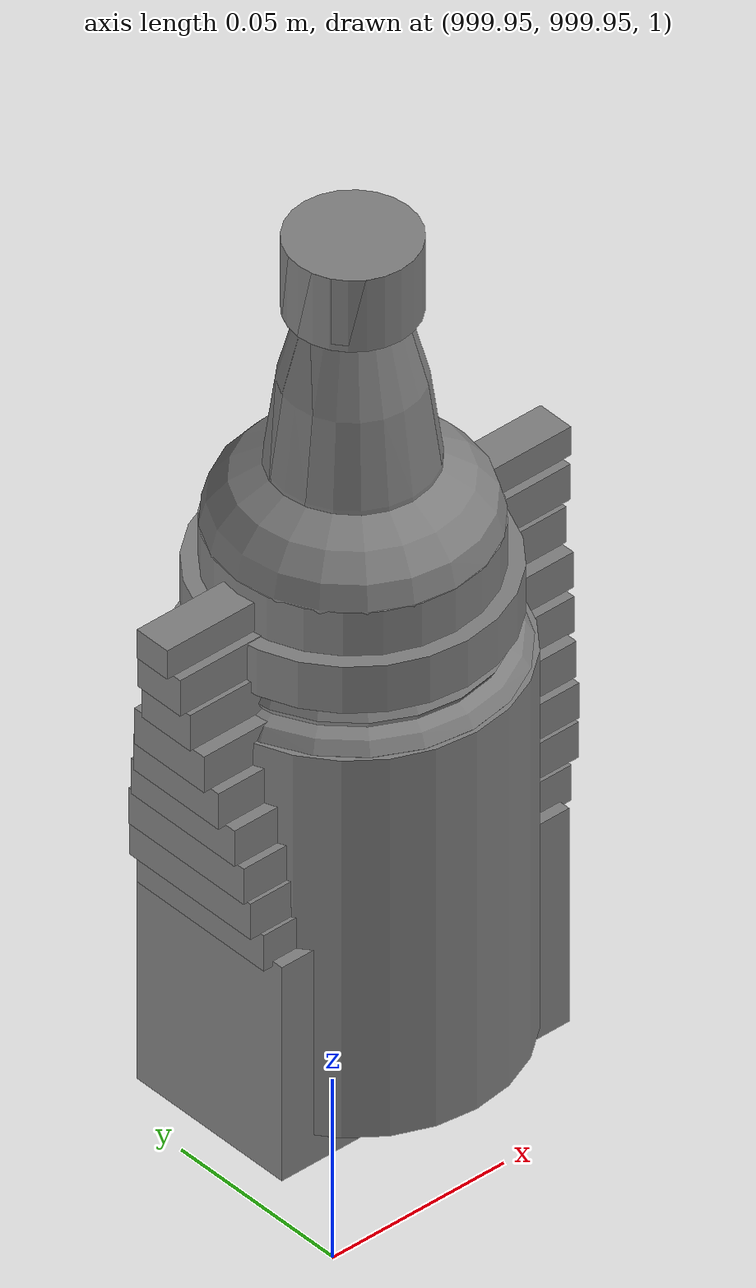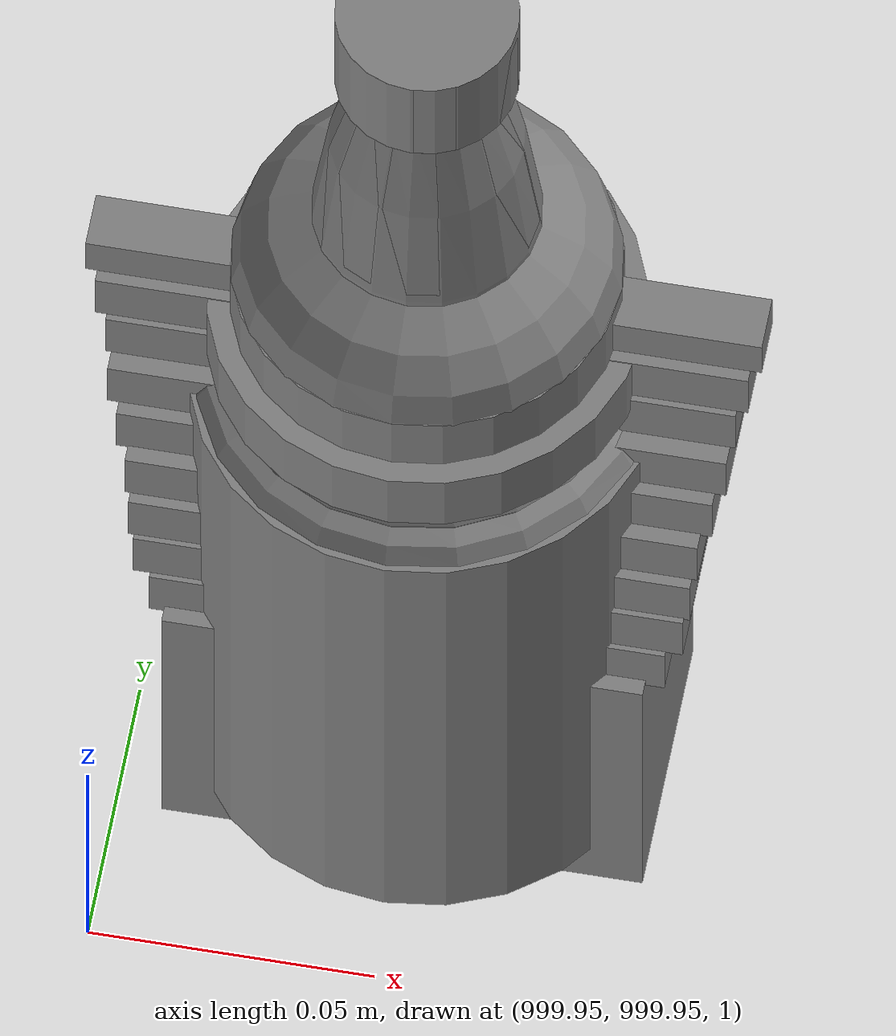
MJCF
<mujoco>
    <option gravity="0.000000000 0.000000000 -9.810000420" timestep="0.0166666" integrator="implicitfast" density="1.225" viscosity="1.8000001e-05" noslip_iterations="10" iterations="100" sdf_iterations="50">
        <flag multiccd="disable"/>
    </option>
    <size memory="1000M"/>
    <compiler coordinate="local"/>
    <worldbody>
        <light cutoff="30" pos="0 1 1" dir="0 -1 -2"/>
        <light cutoff="30" pos="0 -1 1" dir="0 1 -2"/>
        <body pos="0.000000000 0.000000000 0.000000000" euler="0.000000000 0.000000000 0.000000000" name="Interactive Objects_Interactive Objects"/>
        <body pos="1000.000000000 1000.000000000 1.000000000" euler="0.000000000 0.000000000 0.000000000" name="openloong_gripper_2f85_fix_base_usda_jar_01">
            <geom contype="1" conaffinity="1" density="1000" type="box" material="" rgba="0.500000000 0.500000000 0.500000000 1.000000000" solimp="0.899999976 0.949999988 0.001000000" friction="1.000000000 0.005000000 0.000100000" solref="0.020000000 1.000000000" margin="0" condim="3" group="0" pos="0.000000000 0.000000000 0.006158113" quat="1.000000000 0.000000000 0.000000000 0.000000000" size="0.020000000 0.020000000 0.005000000" name="openloong_gripper_2f85_fix_base_usda_geom_1F3D81C2_2944_4B82_BF18_A58309CEA8C5"/>
            <geom contype="1" conaffinity="1" density="1000" type="cylinder" material="" rgba="0.500000000 0.500000000 0.500000000 1.000000000" solimp="0.899999976 0.949999988 0.001000000" friction="1.000000000 0.005000000 0.000100000" solref="0.020000000 1.000000000" margin="0" condim="3" group="0" pos="0.000000000 0.000000000 0.062744498" quat="1.000000000 0.000000000 0.000000000 0.000000000" size="0.041000001 0.052999999 1.000000000" name="openloong_gripper_2f85_fix_base_usda_geom_C0738CA4_669C_4FF3_ADC1_B5EB1713602E"/>
            <geom contype="1" conaffinity="1" density="1000" type="ellipsoid" material="" rgba="0.500000000 0.500000000 0.500000000 1.000000000" solimp="0.899999976 0.949999988 0.001000000" friction="1.000000000 0.005000000 0.000100000" solref="0.020000000 1.000000000" margin="0" condim="3" group="0" pos="0.000000000 0.000000000 0.122252703" quat="1.000000000 0.000000000 0.000000000 0.000000000" size="0.035999998 0.035999998 0.010000000" name="openloong_gripper_2f85_fix_base_usda_geom_ACEBA849_C53B_48DB_A4FD_E1CDB31D209C"/>
            <geom contype="1" conaffinity="1" density="1000" type="cylinder" material="" rgba="0.500000000 0.500000000 0.500000000 1.000000000" solimp="0.899999976 0.949999988 0.001000000" friction="1.000000000 0.005000000 0.000100000" solref="0.020000000 1.000000000" margin="0" condim="3" group="0" pos="0.000000000 0.000000000 0.015747190" quat="1.000000000 0.000000000 0.000000000 0.000000000" size="0.035000000 0.010000000 1.000000000" name="openloong_gripper_2f85_fix_base_usda_geom_98F14CE2_4A35_4A36_9631_3846657F050F"/>
            <geom contype="1" conaffinity="1" density="1000" type="ellipsoid" material="" rgba="0.500000000 0.500000000 0.500000000 1.000000000" solimp="0.899999976 0.949999988 0.001000000" friction="1.000000000 0.005000000 0.000100000" solref="0.020000000 1.000000000" margin="0" condim="3" group="0" pos="0.000000000 0.000000000 0.115815401" quat="1.000000000 0.000000000 0.000000000 0.000000000" size="0.039999999 0.039999999 0.010000000" name="openloong_gripper_2f85_fix_base_usda_geom_02617AA3_77D7_4CF3_82CD_43A0BABAABCE"/>
            <geom contype="1" conaffinity="1" density="1000" type="cylinder" material="" rgba="0.500000000 0.500000000 0.500000000 1.000000000" solimp="0.899999976 0.949999988 0.001000000" friction="1.000000000 0.005000000 0.000100000" solref="0.020000000 1.000000000" margin="0" condim="3" group="0" pos="0.000000000 0.000000000 0.133183479" quat="1.000000000 0.000000000 0.000000000 0.000000000" size="0.037999999 0.006500000 1.000000000" name="openloong_gripper_2f85_fix_base_usda_geom_2E3D5880_4E6E_4460_A4A1_CE73D346A4A8"/>
            <freejoint name="openloong_gripper_2f85_fix_base_usda_jar_01_joint"/>
            <site size="0.005000000 0.005000000 0.005000000" rgba="0.500000000 0.500000000 0.500000000 1.000000000" pos="0.000000000 0.000000000 0.000000000" quat="1.000000000 0.000000000 0.000000000 0.000000000" group="0" type="sphere" name="openloong_gripper_2f85_fix_base_usda_jar_01site"/>
        </body>
        <body pos="1000.000000000 1000.000000000 1.000000000" euler="0.000000000 0.000000000 0.000000000" name="openloong_gripper_2f85_fix_base_usda_bottle_red">
            <geom contype="1" conaffinity="1" density="1000" type="ellipsoid" material="" rgba="0.500000000 0.500000000 0.500000000 1.000000000" solimp="0.899999976 0.949999988 0.001000000" friction="1.000000000 0.005000000 0.000100000" solref="0.020000000 1.000000000" margin="0" condim="3" group="0" pos="0.000000000 0.000000000 0.144284487" quat="1.000000000 0.000000000 0.000000000 0.000000000" size="0.021000000 0.021000000 0.079999998" name="openloong_gripper_2f85_fix_base_usda_geom_E1B34C77_C9E2_4A4E_A63E_BC0E16BC1161"/>
            <geom contype="1" conaffinity="1" density="1000" type="cylinder" material="" rgba="0.500000000 0.500000000 0.500000000 1.000000000" solimp="0.899999976 0.949999988 0.001000000" friction="1.000000000 0.005000000 0.000100000" solref="0.020000000 1.000000000" margin="0" condim="3" group="0" pos="0.000000000 0.000000000 0.220618963" quat="1.000000000 0.000000000 0.000000000 0.000000000" size="0.016000001 0.010000000 1.000000000" name="openloong_gripper_2f85_fix_base_usda_geom_69B11B99_8E45_4DA6_B0C0_2AB0F894501C"/>
            <geom contype="1" conaffinity="1" density="1000" type="ellipsoid" material="" rgba="0.500000000 0.500000000 0.500000000 1.000000000" solimp="0.899999976 0.949999988 0.001000000" friction="1.000000000 0.005000000 0.000100000" solref="0.020000000 1.000000000" margin="0" condim="3" group="0" pos="0.000000000 0.000000000 0.118945479" quat="1.000000000 0.000000000 0.000000000 0.000000000" size="0.030999999 0.030999999 0.029999999" name="openloong_gripper_2f85_fix_base_usda_geom_3EDEC826_D947_44DC_9E8C_0C64F7745EDF"/>
            <geom contype="1" conaffinity="1" density="1000" type="box" material="" rgba="0.500000000 0.500000000 0.500000000 1.000000000" solimp="0.899999976 0.949999988 0.001000000" friction="1.000000000 0.005000000 0.000100000" solref="0.020000000 1.000000000" margin="0" condim="3" group="0" pos="0.000000000 0.000000000 0.002189159" quat="1.000000000 0.000000000 0.000000000 0.000000000" size="0.020000000 0.020000000 0.003000000" name="openloong_gripper_2f85_fix_base_usda_geom_6D5F2313_B299_41E6_9C57_D8FA28DA377B"/>
            <geom contype="1" conaffinity="1" density="1000" type="cylinder" material="" rgba="0.500000000 0.500000000 0.500000000 1.000000000" solimp="0.899999976 0.949999988 0.001000000" friction="1.000000000 0.005000000 0.000100000" solref="0.020000000 1.000000000" margin="0" condim="3" group="0" pos="0.000000000 -0.000366211 0.060884237" quat="1.000000000 0.000000000 0.000000000 0.000000000" size="0.030999999 0.057999998 1.000000000" name="openloong_gripper_2f85_fix_base_usda_geom_7AA6E5AD_0489_4C8B_8216_D13FB5707BDE"/>
            <freejoint name="openloong_gripper_2f85_fix_base_usda_bottle_red_joint"/>
            <site size="0.005000000 0.005000000 0.005000000" rgba="0.500000000 0.500000000 0.500000000 1.000000000" pos="0.000000000 0.000000000 0.000000000" quat="0.999961913 0.008726535 0.000000000 0.000000000" group="0" type="sphere" name="openloong_gripper_2f85_fix_base_usda_bottle_redsite"/>
        </body>
        <body pos="1000.000000000 1000.000000000 1.000000000" euler="0.000000000 0.000000000 0.000000000" name="openloong_gripper_2f85_fix_base_usda_bottle_blue">
            <geom contype="1" conaffinity="1" density="1000" type="ellipsoid" material="" rgba="0.500000000 0.500000000 0.500000000 1.000000000" solimp="0.899999976 0.949999988 0.001000000" friction="1.000000000 0.005000000 0.000100000" solref="0.020000000 1.000000000" margin="0" condim="3" group="0" pos="0.000000000 0.000000000 0.118920922" quat="1.000000000 0.000000000 0.000000000 0.000000000" size="0.030999999 0.030999999 0.029999999" name="openloong_gripper_2f85_fix_base_usda_geom_5BDA7874_4D10_4D8E_98FB_1F711373BC89"/>
            <geom contype="1" conaffinity="1" density="1000" type="box" material="" rgba="0.500000000 0.500000000 0.500000000 1.000000000" solimp="0.899999976 0.949999988 0.001000000" friction="1.000000000 0.005000000 0.000100000" solref="0.020000000 1.000000000" margin="0" condim="3" group="0" pos="0.000000000 0.000000000 0.002164602" quat="1.000000000 0.000000000 0.000000000 0.000000000" size="0.020000000 0.020000000 0.003000000" name="openloong_gripper_2f85_fix_base_usda_geom_E2BE7F48_33C6_4A1F_88F3_D94C7D0DEF68"/>
            <geom contype="1" conaffinity="1" density="1000" type="cylinder" material="" rgba="0.500000000 0.500000000 0.500000000 1.000000000" solimp="0.899999976 0.949999988 0.001000000" friction="1.000000000 0.005000000 0.000100000" solref="0.020000000 1.000000000" margin="0" condim="3" group="0" pos="0.000000000 -0.000366211 0.060859680" quat="1.000000000 0.000000000 0.000000000 0.000000000" size="0.030999999 0.057999998 1.000000000" name="openloong_gripper_2f85_fix_base_usda_geom_E6F854A7_4A81_4418_AB24_DCE25D6D3948"/>
            <geom contype="1" conaffinity="1" density="1000" type="cylinder" material="" rgba="0.500000000 0.500000000 0.500000000 1.000000000" solimp="0.899999976 0.949999988 0.001000000" friction="1.000000000 0.005000000 0.000100000" solref="0.020000000 1.000000000" margin="0" condim="3" group="0" pos="0.000000000 0.000000000 0.220594406" quat="1.000000000 0.000000000 0.000000000 0.000000000" size="0.016000001 0.010000000 1.000000000" name="openloong_gripper_2f85_fix_base_usda_geom_689D5E7E_7588_4134_BEA3_2EB5E17FC32E"/>
            <geom contype="1" conaffinity="1" density="1000" type="ellipsoid" material="" rgba="0.500000000 0.500000000 0.500000000 1.000000000" solimp="0.899999976 0.949999988 0.001000000" friction="1.000000000 0.005000000 0.000100000" solref="0.020000000 1.000000000" margin="0" condim="3" group="0" pos="0.000000000 0.000000000 0.144259930" quat="1.000000000 0.000000000 0.000000000 0.000000000" size="0.021000000 0.021000000 0.079999998" name="openloong_gripper_2f85_fix_base_usda_geom_7CCB34DC_FD9B_4598_AACA_34250905AC7C"/>
            <freejoint name="openloong_gripper_2f85_fix_base_usda_bottle_blue_joint"/>
            <site size="0.005000000 0.005000000 0.005000000" rgba="0.500000000 0.500000000 0.500000000 1.000000000" pos="0.000000000 0.000000000 0.000000000" quat="0.999961913 0.008726535 0.000000000 0.000000000" group="0" type="sphere" name="openloong_gripper_2f85_fix_base_usda_bottle_bluesite"/>
        </body>
        <body pos="-1.820796013 6.622509480 1.770434499" euler="28.357355118 23.583097458 117.855751038" mocap="true" name="spotlight6_SpotLight"/>
        <body pos="1000.000000000 1000.000000000 1.000000000" euler="0.000000000 0.000000000 0.000000000" name="openloong_gripper_2f85_fix_base_usda_can">
            <geom contype="1" conaffinity="1" density="1000" type="cylinder" material="" rgba="0.500000000 0.500000000 0.500000000 1.000000000" solimp="0.899999976 0.949999988 0.001000000" friction="1.000000000 0.005000000 0.000100000" solref="0.020000000 1.000000000" margin="0" condim="3" group="0" pos="0.000000000 0.000000000 0.079676986" quat="1.000000000 0.000000000 0.000000000 0.000000000" size="0.034000002 0.071999997 1.000000000" name="openloong_gripper_2f85_fix_base_usda_geom_81DC856E_A65E_46D0_9932_58FA5B2CE6ED"/>
            <geom contype="1" conaffinity="1" density="1000" type="ellipsoid" material="" rgba="0.500000000 0.500000000 0.500000000 1.000000000" solimp="0.899999976 0.949999988 0.001000000" friction="1.000000000 0.005000000 0.000100000" solref="0.020000000 1.000000000" margin="0" condim="3" group="0" pos="0.000000000 0.000000000 0.151854277" quat="1.000000000 0.000000000 0.000000000 0.000000000" size="0.034000002 0.034000002 0.020000000" name="openloong_gripper_2f85_fix_base_usda_geom_CD372132_CA14_469D_81E7_68E3642FC246"/>
            <geom contype="1" conaffinity="1" density="1000" type="box" material="" rgba="0.500000000 0.500000000 0.500000000 1.000000000" solimp="0.899999976 0.949999988 0.001000000" friction="1.000000000 0.005000000 0.000100000" solref="0.020000000 1.000000000" margin="0" condim="3" group="0" pos="0.000000000 0.000000000 0.004777670" quat="1.000000000 0.000000000 0.000000000 0.000000000" size="0.020000000 0.020000000 0.005000000" name="openloong_gripper_2f85_fix_base_usda_geom_7229A4ED_5C48_4C81_82C3_2160640E6C7F"/>
            <freejoint name="openloong_gripper_2f85_fix_base_usda_can_joint"/>
            <site size="0.005000000 0.005000000 0.005000000" rgba="0.500000000 0.500000000 0.500000000 1.000000000" pos="0.000000000 0.000000000 0.000000000" quat="1.000000000 0.000000000 0.000000000 0.000000000" group="0" type="sphere" name="openloong_gripper_2f85_fix_base_usda_cansite"/>
        </body>
        <body pos="1000.000000000 1000.000000000 1.000000000" euler="0.000000000 0.000000000 0.000000000" name="openloong_gripper_2f85_fix_base_usda_salt">
            <geom contype="1" conaffinity="1" density="1000" type="box" material="" rgba="0.500000000 0.500000000 0.500000000 1.000000000" solimp="0.899999976 0.949999988 0.001000000" friction="1.000000000 0.005000000 0.000100000" solref="0.020000000 1.000000000" margin="0" condim="3" group="0" pos="0.000305176 0.000000000 0.084862232" quat="1.000000000 0.000000000 0.000000000 0.000000000" size="0.048999999 0.018999999 0.005000000" name="openloong_gripper_2f85_fix_base_usda_geom_4732A910_7507_417A_A31A_F06DD997D6AC"/>
            <geom contype="1" conaffinity="1" density="1000" type="box" material="" rgba="0.500000000 0.500000000 0.500000000 1.000000000" solimp="0.899999976 0.949999988 0.001000000" friction="1.000000000 0.005000000 0.000100000" solref="0.020000000 1.000000000" margin="0" condim="3" group="0" pos="0.000305176 0.000000000 0.104564309" quat="1.000000000 0.000000000 0.000000000 0.000000000" size="0.052000001 0.014000000 0.005000000" name="openloong_gripper_2f85_fix_base_usda_geom_560E21D0_43AB_4298_8BF5_403DF5F639E5"/>
            <geom contype="1" conaffinity="1" density="1000" type="box" material="" rgba="0.500000000 0.500000000 0.500000000 1.000000000" solimp="0.899999976 0.949999988 0.001000000" friction="1.000000000 0.005000000 0.000100000" solref="0.020000000 1.000000000" margin="0" condim="3" group="0" pos="0.000305176 0.000000000 0.114487171" quat="1.000000000 0.000000000 0.000000000 0.000000000" size="0.054000001 0.011500000 0.005000000" name="openloong_gripper_2f85_fix_base_usda_geom_CFE06F64_83C5_4301_92ED_99E101263404"/>
            <geom contype="1" conaffinity="1" density="1000" type="box" material="" rgba="0.500000000 0.500000000 0.500000000 1.000000000" solimp="0.899999976 0.949999988 0.001000000" friction="1.000000000 0.005000000 0.000100000" solref="0.020000000 1.000000000" margin="0" condim="3" group="0" pos="0.000305176 0.000000000 0.075103164" quat="1.000000000 0.000000000 0.000000000 0.000000000" size="0.048000000 0.020000000 0.005000000" name="openloong_gripper_2f85_fix_base_usda_geom_0E518997_C973_4198_AF88_5FA554604513"/>
            <geom contype="1" conaffinity="1" density="1000" type="box" material="" rgba="0.500000000 0.500000000 0.500000000 1.000000000" solimp="0.899999976 0.949999988 0.001000000" friction="1.000000000 0.005000000 0.000100000" solref="0.020000000 1.000000000" margin="0" condim="3" group="0" pos="0.000305176 0.000000000 0.134892464" quat="1.000000000 0.000000000 0.000000000 0.000000000" size="0.057000000 0.007000000 0.005000000" name="openloong_gripper_2f85_fix_base_usda_geom_040AF358_CE5B_467E_8122_158FA2CFEF34"/>
            <geom contype="1" conaffinity="1" density="1000" type="box" material="" rgba="0.500000000 0.500000000 0.500000000 1.000000000" solimp="0.899999976 0.949999988 0.001000000" friction="1.000000000 0.005000000 0.000100000" solref="0.020000000 1.000000000" margin="0" condim="3" group="0" pos="0.000305176 0.000000000 0.094920278" quat="1.000000000 0.000000000 0.000000000 0.000000000" size="0.050000001 0.017000001 0.005000000" name="openloong_gripper_2f85_fix_base_usda_geom_7DDB7366_7A6E_4E4D_A1A4_0A05D94F839C"/>
            <geom contype="1" conaffinity="1" density="1000" type="box" material="" rgba="0.500000000 0.500000000 0.500000000 1.000000000" solimp="0.899999976 0.949999988 0.001000000" friction="1.000000000 0.005000000 0.000100000" solref="0.020000000 1.000000000" margin="0" condim="3" group="0" pos="0.000305176 0.000000000 0.065204859" quat="1.000000000 0.000000000 0.000000000 0.000000000" size="0.045000002 0.021000000 0.005000000" name="openloong_gripper_2f85_fix_base_usda_geom_1AF9C6A1_E742_40BB_8745_BCADF9CFA6BA"/>
            <geom contype="1" conaffinity="1" density="1000" type="box" material="" rgba="0.500000000 0.500000000 0.500000000 1.000000000" solimp="0.899999976 0.949999988 0.001000000" friction="1.000000000 0.005000000 0.000100000" solref="0.020000000 1.000000000" margin="0" condim="3" group="0" pos="0.000305176 0.000000000 0.144135714" quat="1.000000000 0.000000000 0.000000000 0.000000000" size="0.059000000 0.005000000 0.004000000" name="openloong_gripper_2f85_fix_base_usda_geom_4D7B401A_ED76_42B0_A202_22AC5C6FAEA1"/>
            <geom contype="1" conaffinity="1" density="1000" type="box" material="" rgba="0.500000000 0.500000000 0.500000000 1.000000000" solimp="0.899999976 0.949999988 0.001000000" friction="1.000000000 0.005000000 0.000100000" solref="0.020000000 1.000000000" margin="0" condim="3" group="0" pos="0.000000000 0.000000000 0.031593561" quat="1.000000000 0.000000000 0.000000000 0.000000000" size="0.041999999 0.024000000 0.029999999" name="openloong_gripper_2f85_fix_base_usda_geom_E2213319_1F13_48FD_BC9E_578A8B20E16B"/>
            <geom contype="1" conaffinity="1" density="1000" type="box" material="" rgba="0.500000000 0.500000000 0.500000000 1.000000000" solimp="0.899999976 0.949999988 0.001000000" friction="1.000000000 0.005000000 0.000100000" solref="0.020000000 1.000000000" margin="0" condim="3" group="0" pos="0.000305176 0.000000000 0.124608755" quat="1.000000000 0.000000000 0.000000000 0.000000000" size="0.055000000 0.008000000 0.005000000" name="openloong_gripper_2f85_fix_base_usda_geom_6311BA6D_CB0B_42C5_84FA_C5B233EFFC8E"/>
            <freejoint name="openloong_gripper_2f85_fix_base_usda_salt_joint"/>
            <site size="0.005000000 0.005000000 0.005000000" rgba="0.500000000 0.500000000 0.500000000 1.000000000" pos="0.000000000 0.000000000 0.000000000" quat="1.000000000 0.000000000 0.000000000 0.000000000" group="0" type="sphere" name="openloong_gripper_2f85_fix_base_usda_saltsite"/>
        </body>
        <body pos="-2.043624401 6.135759830 1.833680272" euler="8.372198105 77.602005005 -115.141960144" mocap="true" name="spotlight3_SpotLight"/>
        <body pos="-2.025240898 6.016537666 1.811890006" euler="-129.139526367 -44.892616272 99.971824646" mocap="true" name="spotlight5_SpotLight"/>
        <body pos="0.000000000 0.000000000 0.000000000" euler="0.000000000 0.000000000 0.000000000" name=" Static Objects_ Static Objects">
            <geom contype="1" conaffinity="1" density="1000" type="box" material="" rgba="0.500000000 0.500000000 0.500000000 1.000000000" solimp="0.899999976 0.949999988 0.001000000" friction="1.000000000 0.005000000 0.000100000" solref="0.020000000 1.000000000" margin="0" condim="3" group="0" pos="-6.286010742 6.153595448 1.563861728" quat="0.707107067 0.000000000 0.000000000 0.707106471" size="0.529999971 3.134999990 0.025000000" name=" Static Objects_geom_E22845F1_5277_4003_9437_B69E8A0F8C6C"/>
            <geom contype="1" conaffinity="1" density="1000" type="box" material="" rgba="0.500000000 0.500000000 0.500000000 1.000000000" solimp="0.899999976 0.949999988 0.001000000" friction="1.000000000 0.005000000 0.000100000" solref="0.020000000 1.000000000" margin="0" condim="3" group="0" pos="-3.101639986 6.150595188 1.018643856" quat="1.000000000 0.000000000 0.000000000 0.000000000" size="0.050000001 0.579999983 1.019999981" name=" Static Objects_geom_D3B4F3E1_1B82_41FE_A31E_F65C2F978B63"/>
            <geom contype="1" conaffinity="1" density="1000" type="box" material="" rgba="0.500000000 0.500000000 0.500000000 1.000000000" solimp="0.899999976 0.949999988 0.001000000" friction="1.000000000 0.005000000 0.000100000" solref="0.020000000 1.000000000" margin="0" condim="3" group="0" pos="-2.825197220 6.153595448 1.563861728" quat="0.707107067 0.000000000 0.000000000 0.707106471" size="0.550000012 0.239999995 0.025000000" name=" Static Objects_geom_F7828A89_4261_4AAE_A4DC_18BFE6170046"/>
            <geom contype="1" conaffinity="1" density="1000" type="box" material="" rgba="0.500000000 0.500000000 0.500000000 1.000000000" solimp="0.899999976 0.949999988 0.001000000" friction="1.000000000 0.005000000 0.000100000" solref="0.020000000 1.000000000" margin="0" condim="3" group="0" pos="-6.311686516 6.153595448 1.018643856" quat="0.707107067 0.000000000 0.000000000 0.707106471" size="0.050000001 3.150000095 1.019999981" name=" Static Objects_geom_2A942DE2_67AE_47F1_B3A6_B62964098605"/>
            <geom contype="1" conaffinity="1" density="1000" type="box" material="" rgba="0.500000000 0.500000000 0.500000000 1.000000000" solimp="0.899999976 0.949999988 0.001000000" friction="1.000000000 0.005000000 0.000100000" solref="0.020000000 1.000000000" margin="0" condim="3" group="0" pos="-2.825197220 6.153595448 1.115278244" quat="0.707107067 0.000000000 0.000000000 0.707106471" size="0.550000012 0.239999995 0.025000000" name=" Static Objects_geom_18C5B9E7_9B8D_450E_84E3_11F323BFEA0F"/>
            <geom contype="1" conaffinity="1" density="1000" type="box" material="" rgba="0.500000000 0.500000000 0.500000000 1.000000000" solimp="0.899999976 0.949999988 0.001000000" friction="1.000000000 0.005000000 0.000100000" solref="0.020000000 1.000000000" margin="0" condim="3" group="0" pos="-6.293097973 6.153595448 1.114443064" quat="0.707107067 0.000000000 0.000000000 0.707106471" size="0.529999971 3.134999990 0.025000000" name=" Static Objects_geom_AA825110_6AEF_4D32_B421_B4813488E1A5"/>
            <geom contype="1" conaffinity="1" density="1000" type="box" material="" rgba="0.500000000 0.500000000 0.500000000 1.000000000" solimp="0.899999976 0.949999988 0.001000000" friction="1.000000000 0.005000000 0.000100000" solref="0.020000000 1.000000000" margin="0" condim="3" group="0" pos="-2.825197220 6.153595448 0.629031777" quat="0.707107067 0.000000000 0.000000000 0.707106471" size="0.550000012 0.239999995 0.025000000" name=" Static Objects_geom_D046DE08_1D00_4337_A445_FAF5AD70ECA6"/>
            <geom contype="1" conaffinity="1" density="1000" type="box" material="" rgba="0.500000000 0.500000000 0.500000000 1.000000000" solimp="0.899999976 0.949999988 0.001000000" friction="1.000000000 0.005000000 0.000100000" solref="0.020000000 1.000000000" margin="0" condim="3" group="0" pos="-6.286010742 6.153595448 0.096129179" quat="0.707107067 0.000000000 0.000000000 0.707106471" size="0.529999971 3.134999990 0.098999999" name=" Static Objects_geom_F892F6C4_C8E3_432B_AA2D_5010F22FD6DA"/>
            <geom contype="1" conaffinity="1" density="1000" type="box" material="" rgba="0.500000000 0.500000000 0.500000000 1.000000000" solimp="0.899999976 0.949999988 0.001000000" friction="1.000000000 0.005000000 0.000100000" solref="0.020000000 1.000000000" margin="0" condim="3" group="0" pos="-2.825197220 6.153595448 0.097434282" quat="0.707107067 0.000000000 0.000000000 0.707106471" size="0.550000012 0.239999995 0.098999999" name=" Static Objects_geom_68ABB0A8_20F3_4A9F_A82D_58C3C72770BA"/>
            <geom contype="1" conaffinity="1" density="1000" type="box" material="" rgba="0.500000000 0.500000000 0.500000000 1.000000000" solimp="0.899999976 0.949999988 0.001000000" friction="1.000000000 0.005000000 0.000100000" solref="0.020000000 1.000000000" margin="0" condim="3" group="0" pos="-6.286010742 6.153595448 0.629031777" quat="0.707107067 0.000000000 0.000000000 0.707106471" size="0.529999971 3.134999990 0.025000000" name=" Static Objects_geom_81AC058F_E77A_43D0_9EE5_34443F685132"/>
            <geom contype="1" conaffinity="1" density="1000" type="box" material="" rgba="0.500000000 0.500000000 0.500000000 1.000000000" solimp="0.899999976 0.949999988 0.001000000" friction="1.000000000 0.005000000 0.000100000" solref="0.020000000 1.000000000" margin="0" condim="3" group="0" pos="-6.000000000 20.159999847 2.000000000" quat="1.000000000 0.000000000 0.000000000 0.000000000" size="6.079999924 0.070000000 2.000000000" name=" Static Objects_geom_4085461E_55D7_43F6_887A_07214F6CB74B"/>
            <geom contype="1" conaffinity="1" density="1000" type="box" material="" rgba="0.500000000 0.500000000 0.500000000 1.000000000" solimp="0.899999976 0.949999988 0.001000000" friction="1.000000000 0.005000000 0.000100000" solref="0.020000000 1.000000000" margin="0" condim="3" group="0" pos="-6.000000000 0.035000000 2.000000000" quat="1.000000000 0.000000000 0.000000000 0.000000000" size="6.079999924 0.070000000 2.000000000" name=" Static Objects_geom_44A1EE43_8FF8_4B1B_AB9A_5C4E4051E2E5"/>
            <geom contype="1" conaffinity="1" density="1000" type="box" material="" rgba="0.500000000 0.500000000 0.500000000 1.000000000" solimp="0.899999976 0.949999988 0.001000000" friction="1.000000000 0.005000000 0.000100000" solref="0.020000000 1.000000000" margin="0" condim="3" group="0" pos="0.000000000 10.000000000 2.000000000" quat="1.000000000 0.000000000 0.000000000 0.000000000" size="0.070000000 10.500000000 2.000000000" name=" Static Objects_geom_1DB6E72E_20D3_4FDC_8BA9_26295EE0C431"/>
            <geom contype="1" conaffinity="1" density="1000" type="box" material="" rgba="0.500000000 0.500000000 0.500000000 1.000000000" solimp="0.899999976 0.949999988 0.001000000" friction="1.000000000 0.005000000 0.000100000" solref="0.020000000 1.000000000" margin="0" condim="3" group="0" pos="-12.050000191 10.000000000 2.000000000" quat="1.000000000 0.000000000 0.000000000 0.000000000" size="0.070000000 10.500000000 2.000000000" name=" Static Objects_geom_D059B79D_45CF_4FBA_A059_985E6ADB2C5B"/>
            <geom contype="1" conaffinity="1" density="1000" type="plane" material="" rgba="0.500000000 0.500000000 0.500000000 1.000000000" solimp="0.899999976 0.949999988 0.001000000" friction="1.000000000 0.005000000 0.000100000" solref="0.020000000 1.000000000" margin="0" condim="3" group="0" pos="-6.000000000 10.399999619 0.000000000" quat="1.000000000 0.000000000 0.000000000 0.000000000" size="6.050000191 10.800000191 0.010000000" name=" Static Objects_geom_B5582E2A_684E_47BA_A4AD_45A90F5879A4"/>
            <geom contype="1" conaffinity="1" density="1000" type="box" material="" rgba="0.500000000 0.500000000 0.500000000 1.000000000" solimp="0.899999976 0.949999988 0.001000000" friction="1.000000000 0.005000000 0.000100000" solref="0.020000000 1.000000000" margin="0" condim="3" group="0" pos="-8.830721855 2.096410990 0.549305558" quat="1.000000000 0.000000000 0.000000000 0.000000000" size="0.280000001 0.430000007 0.550000012" name=" Static Objects_geom_9BAA5530_BD63_488D_8D89_DE03426B2400"/>
            <geom contype="1" conaffinity="1" density="1000" type="box" material="" rgba="0.500000000 0.500000000 0.500000000 1.000000000" solimp="0.899999976 0.949999988 0.001000000" friction="1.000000000 0.005000000 0.000100000" solref="0.020000000 1.000000000" margin="0" condim="3" group="0" pos="-6.460197449 2.937205315 0.548931718" quat="1.000000000 0.000000000 0.000000000 0.000000000" size="2.650000095 0.430000007 0.550000012" name=" Static Objects_geom_464271AA_99E1_4DEC_BB4D_B89B90AC9833"/>
            <geom contype="1" conaffinity="1" density="1000" type="box" material="" rgba="0.500000000 0.500000000 0.500000000 1.000000000" solimp="0.899999976 0.949999988 0.001000000" friction="1.000000000 0.005000000 0.000100000" solref="0.020000000 1.000000000" margin="0" condim="3" group="0" pos="-4.240264893 1.327049494 0.549888909" quat="1.000000000 0.000000000 0.000000000 0.000000000" size="0.430000007 1.200000048 0.550000012" name=" Static Objects_geom_F90BB945_AAF9_46A5_A346_EABFC920538F"/>
            <geom contype="1" conaffinity="1" density="1000" type="box" material="" rgba="0.500000000 0.500000000 0.500000000 1.000000000" solimp="0.899999976 0.949999988 0.001000000" friction="1.000000000 0.005000000 0.000100000" solref="0.020000000 1.000000000" margin="0" condim="3" group="0" pos="-7.408766270 3.088089943 1.776644945" quat="0.928051054 0.000000000 0.000000000 0.372453064" size="0.050000001 0.100000001 0.050000001" name=" Static Objects_geom_EEE3788F_942F_450D_B951_8D4EA9116C94"/>
            <geom contype="1" conaffinity="1" density="1000" type="box" material="" rgba="0.500000000 0.500000000 0.500000000 1.000000000" solimp="0.899999976 0.949999988 0.001000000" friction="1.000000000 0.005000000 0.000100000" solref="0.020000000 1.000000000" margin="0" condim="3" group="0" pos="-7.437745571 3.067511320 1.289965630" quat="1.000000000 0.000000000 0.000000000 0.000000000" size="0.029999999 0.020000000 0.020000000" name=" Static Objects_geom_A832AA8B_5E4D_447B_9F3B_CCAAEB910E57"/>
            <geom contype="1" conaffinity="1" density="1000" type="box" material="" rgba="0.500000000 0.500000000 0.500000000 1.000000000" solimp="0.899999976 0.949999988 0.001000000" friction="1.000000000 0.005000000 0.000100000" solref="0.020000000 1.000000000" margin="0" condim="3" group="0" pos="-7.719123363 2.867671013 1.173410416" quat="1.000000000 0.000000000 0.000000000 0.000000000" size="0.250000000 0.250000000 0.079999998" name=" Static Objects_geom_6EF0C98C_32B5_4436_B295_EA8AB373CFCD"/>
            <geom contype="1" conaffinity="1" density="1000" type="box" material="" rgba="0.500000000 0.500000000 0.500000000 1.000000000" solimp="0.899999976 0.949999988 0.001000000" friction="1.000000000 0.005000000 0.000100000" solref="0.020000000 1.000000000" margin="0" condim="3" group="0" pos="-7.719123363 2.958004713 1.530241251" quat="1.000000000 0.000000000 0.000000000 0.000000000" size="0.250000000 0.159999996 0.280000001" name=" Static Objects_geom_98CD25BA_8DD0_43B3_B9E7_843A14B31B60"/>
            <geom contype="1" conaffinity="1" density="1000" type="cylinder" material="" rgba="0.500000000 0.500000000 0.500000000 1.000000000" solimp="0.899999976 0.949999988 0.001000000" friction="1.000000000 0.005000000 0.000100000" solref="0.020000000 1.000000000" margin="0" condim="3" group="0" pos="-7.427312374 3.069516420 1.502544641" quat="0.928051054 0.000000000 0.000000000 0.372453064" size="0.015000000 0.230000004 0.100000001" name=" Static Objects_geom_120316DE_10F7_4A03_AD9C_B8D445FBD716"/>
            <geom contype="1" conaffinity="1" density="1000" type="box" material="" rgba="0.500000000 0.500000000 0.500000000 1.000000000" solimp="0.899999976 0.949999988 0.001000000" friction="1.000000000 0.005000000 0.000100000" solref="0.020000000 1.000000000" margin="0" condim="3" group="0" pos="-9.058088303 6.434794426 1.209077358" quat="1.000000000 0.000000000 0.000000000 0.000000000" size="0.250000000 0.100000001 0.070000000" name=" Static Objects_geom_AB533085_2ED3_4C9E_BA14_DDAB8C3245C3"/>
            <geom contype="1" conaffinity="1" density="1000" type="box" material="" rgba="0.500000000 0.500000000 0.500000000 1.000000000" solimp="0.899999976 0.949999988 0.001000000" friction="1.000000000 0.005000000 0.000100000" solref="0.020000000 1.000000000" margin="0" condim="3" group="0" pos="-5.611940861 6.318420410 0.350975692" quat="1.000000000 0.000000000 0.000000000 0.000000000" size="0.699999988 0.100000001 0.150000006" name=" Static Objects_geom_A8B6C4D8_A8C6_4991_81A6_79288F2546A3"/>
            <geom contype="1" conaffinity="1" density="1000" type="box" material="" rgba="0.500000000 0.500000000 0.500000000 1.000000000" solimp="0.899999976 0.949999988 0.001000000" friction="1.000000000 0.005000000 0.000100000" solref="0.020000000 1.000000000" margin="0" condim="3" group="0" pos="-9.237723351 6.464855671 1.209077358" quat="1.000000000 0.000000000 0.000000000 0.000000000" size="0.100000001 0.100000001 0.070000000" name=" Static Objects_geom_6887155F_E477_4614_8A0A_081F10466A65"/>
            <geom contype="1" conaffinity="1" density="1000" type="box" material="" rgba="0.500000000 0.500000000 0.500000000 1.000000000" solimp="0.899999976 0.949999988 0.001000000" friction="1.000000000 0.005000000 0.000100000" solref="0.020000000 1.000000000" margin="0" condim="3" group="0" pos="-6.300771236 6.459744930 1.744376063" quat="1.000000000 0.000000000 0.000000000 0.000000000" size="3.000000000 0.200000003 0.150000006" name=" Static Objects_geom_9D74D0FF_63F4_4F8D_B714_EE68394433F5"/>
            <geom contype="1" conaffinity="1" density="1000" type="box" material="" rgba="0.500000000 0.500000000 0.500000000 1.000000000" solimp="0.899999976 0.949999988 0.001000000" friction="1.000000000 0.005000000 0.000100000" solref="0.020000000 1.000000000" margin="0" condim="3" group="0" pos="-7.373087406 6.458900928 1.214329123" quat="1.000000000 0.000000000 0.000000000 0.000000000" size="0.250000000 0.200000003 0.075000003" name=" Static Objects_geom_118CCBAF_5102_4339_862A_50CC181661CB"/>
            <geom contype="1" conaffinity="1" density="1000" type="box" material="" rgba="0.500000000 0.500000000 0.500000000 1.000000000" solimp="0.899999976 0.949999988 0.001000000" friction="1.000000000 0.005000000 0.000100000" solref="0.020000000 1.000000000" margin="0" condim="3" group="0" pos="-4.035642624 6.459744930 0.352518857" quat="1.000000000 0.000000000 0.000000000 0.000000000" size="0.800000012 0.200000003 0.150000006" name=" Static Objects_geom_C2EB37BA_E4DB_4C4B_8C18_BD2C8F18A209"/>
            <geom contype="1" conaffinity="1" density="1000" type="box" material="" rgba="0.500000000 0.500000000 0.500000000 1.000000000" solimp="0.899999976 0.949999988 0.001000000" friction="1.000000000 0.005000000 0.000100000" solref="0.020000000 1.000000000" margin="0" condim="3" group="0" pos="-3.907610416 6.318625927 0.800981164" quat="1.000000000 0.000000000 0.000000000 0.000000000" size="0.500000000 0.100000001 0.150000006" name=" Static Objects_geom_00DDCB60_2986_41FE_B608_3843CA999923"/>
            <geom contype="1" conaffinity="1" density="1000" type="box" material="" rgba="0.500000000 0.500000000 0.500000000 1.000000000" solimp="0.899999976 0.949999988 0.001000000" friction="1.000000000 0.005000000 0.000100000" solref="0.020000000 1.000000000" margin="0" condim="3" group="0" pos="-6.098561764 6.327973843 1.292199373" quat="1.000000000 0.000000000 0.000000000 0.000000000" size="0.500000000 0.100000001 0.150000006" name=" Static Objects_geom_5723C9F9_C251_44DF_9AFC_87945F782D8B"/>
            <geom contype="1" conaffinity="1" density="1000" type="box" material="" rgba="0.500000000 0.500000000 0.500000000 1.000000000" solimp="0.899999976 0.949999988 0.001000000" friction="1.000000000 0.005000000 0.000100000" solref="0.020000000 1.000000000" margin="0" condim="3" group="0" pos="-7.886891365 6.459744930 0.352518857" quat="1.000000000 0.000000000 0.000000000 0.000000000" size="1.500000000 0.200000003 0.150000006" name=" Static Objects_geom_67B7DE1C_97B6_4637_B846_10562C3D2C6E"/>
            <geom contype="1" conaffinity="1" density="1000" type="box" material="" rgba="0.500000000 0.500000000 0.500000000 1.000000000" solimp="0.899999976 0.949999988 0.001000000" friction="1.000000000 0.005000000 0.000100000" solref="0.020000000 1.000000000" margin="0" condim="3" group="0" pos="-6.824534416 6.447464466 1.212718010" quat="1.000000000 0.000000000 0.000000000 0.000000000" size="0.100000001 0.100000001 0.075000003" name=" Static Objects_geom_C319118D_E076_4CA3_9325_D10E6150D312"/>
            <geom contype="1" conaffinity="1" density="1000" type="box" material="" rgba="0.500000000 0.500000000 0.500000000 1.000000000" solimp="0.899999976 0.949999988 0.001000000" friction="1.000000000 0.005000000 0.000100000" solref="0.020000000 1.000000000" margin="0" condim="3" group="0" pos="-4.407354832 6.459744930 1.292199373" quat="1.000000000 0.000000000 0.000000000 0.000000000" size="1.240000010 0.200000003 0.150000006" name=" Static Objects_geom_8961D886_2F0E_447D_B5EC_6BBFC2AF0414"/>
            <geom contype="1" conaffinity="1" density="1000" type="box" material="" rgba="0.500000000 0.500000000 0.500000000 1.000000000" solimp="0.899999976 0.949999988 0.001000000" friction="1.000000000 0.005000000 0.000100000" solref="0.020000000 1.000000000" margin="0" condim="3" group="0" pos="-6.751636982 6.459744930 0.800981164" quat="1.000000000 0.000000000 0.000000000 0.000000000" size="2.200000048 0.200000003 0.150000006" name=" Static Objects_geom_A4E13276_9F9C_462A_91AA_4AF63AAB30BB"/>
            <geom contype="1" conaffinity="1" density="1000" type="box" material="" rgba="0.500000000 0.500000000 0.500000000 1.000000000" solimp="0.899999976 0.949999988 0.001000000" friction="1.000000000 0.005000000 0.000100000" solref="0.020000000 1.000000000" margin="0" condim="3" group="0" pos="-6.924745083 6.362090111 1.214329123" quat="1.000000000 0.000000000 0.000000000 0.000000000" size="0.200000003 0.100000001 0.075000003" name=" Static Objects_geom_2A511175_2114_419B_B1A7_CEF2269B005F"/>
            <geom contype="1" conaffinity="1" density="1000" type="box" material="" rgba="0.500000000 0.500000000 0.500000000 1.000000000" solimp="0.899999976 0.949999988 0.001000000" friction="1.000000000 0.005000000 0.000100000" solref="0.020000000 1.000000000" margin="0" condim="3" group="0" pos="-8.844120979 6.464855671 1.209077358" quat="1.000000000 0.000000000 0.000000000 0.000000000" size="0.100000001 0.100000001 0.070000000" name=" Static Objects_geom_5934E1F3_E2EC_4679_9163_88F100BC2F05"/>
            <geom contype="1" conaffinity="1" density="1000" type="box" material="" rgba="0.500000000 0.500000000 0.500000000 1.000000000" solimp="0.899999976 0.949999988 0.001000000" friction="1.000000000 0.005000000 0.000100000" solref="0.020000000 1.000000000" margin="0" condim="3" group="0" pos="-3.157672644 6.136868477 1.348373055" quat="1.000000000 0.000000000 0.000000000 0.000000000" size="0.200000003 0.519999981 0.300000012" name=" Static Objects_geom_6388CC63_CEF2_4DDD_9E8D_7C26DFA3E165"/>
        </body>
        <body pos="-6.332345009 2.779978037 1.034067392" euler="0.000000000 0.000000000 0.000000000" name="openloong_gripper_2f85_fix_base_usda_basket">
            <geom contype="1" conaffinity="1" density="100000" type="box" material="" rgba="0.500000000 0.500000000 0.500000000 1.000000000" solimp="0.899999976 0.949999988 0.001000000" friction="1.000000000 0.899999976 0.000100000" solref="0.020000000 1.000000000" margin="0" condim="3" group="0" pos="-0.039724827 -0.188568115 0.167089701" quat="0.997537494 0.070135131 0.000000000 0.000000000" size="0.150000006 0.006000000 0.108000003" name="openloong_gripper_2f85_fix_base_usda_geom_BB7B5DCE_93E2_43BB_9AF9_330ACB5E8191"/>
            <geom contype="1" conaffinity="1" density="100000" type="box" material="" rgba="0.500000000 0.500000000 0.500000000 1.000000000" solimp="0.899999976 0.949999988 0.001000000" friction="1.000000000 0.899999976 0.000100000" solref="0.020000000 1.000000000" margin="0" condim="3" group="0" pos="0.094372749 0.000000000 0.168361664" quat="0.706172049 0.036353335 0.036353379 0.706171215" size="0.200000003 0.006000000 0.108000003" name="openloong_gripper_2f85_fix_base_usda_geom_3AEC9A4B_FFAF_4C29_B698_D2A03407F840"/>
            <geom contype="1" conaffinity="1" density="100000" type="box" material="" rgba="0.500000000 0.500000000 0.500000000 1.000000000" solimp="0.899999976 0.949999988 0.001000000" friction="1.000000000 0.899999976 0.000100000" solref="0.020000000 1.000000000" margin="0" condim="3" group="0" pos="-0.039724827 0.000000000 0.068126202" quat="1.000000000 0.000000000 0.000000000 0.000000000" size="0.129999995 0.174999997 0.006000000" name="openloong_gripper_2f85_fix_base_usda_geom_AFB70B73_83FC_44BA_A1CB_B19FAF721681"/>
            <geom contype="1" conaffinity="1" density="100000" type="box" material="" rgba="0.500000000 0.500000000 0.500000000 1.000000000" solimp="0.899999976 0.949999988 0.001000000" friction="1.000000000 0.899999976 0.000100000" solref="0.020000000 1.000000000" margin="0" condim="3" group="0" pos="-0.039724827 0.188377380 0.167089701" quat="0.997489929 -0.070808925 0.000000000 0.000000000" size="0.150000006 0.006000000 0.108000003" name="openloong_gripper_2f85_fix_base_usda_geom_A23EC769_B598_40AE_926D_93DD86D63BBB"/>
            <geom contype="1" conaffinity="1" density="100000" type="box" material="" rgba="0.500000000 0.500000000 0.500000000 1.000000000" solimp="0.899999976 0.949999988 0.001000000" friction="1.000000000 0.899999976 0.000100000" solref="0.020000000 1.000000000" margin="0" condim="3" group="0" pos="-0.172339439 0.000000000 0.168361664" quat="0.706172407 -0.036353018 -0.036353093 0.706170976" size="0.200000003 0.006000000 0.108000003" name="openloong_gripper_2f85_fix_base_usda_geom_1DAFC2FD_74D5_4C69_98FE_AA090EB35F71"/>
            <freejoint name="openloong_gripper_2f85_fix_base_usda_basket_joint"/>
            <site size="0.005000000 0.005000000 0.005000000" rgba="0.500000000 0.500000000 0.500000000 1.000000000" pos="0.000000000 0.000000000 0.000000000" quat="1.000000000 0.000000000 0.000000000 0.000000000" group="0" type="sphere" name="openloong_gripper_2f85_fix_base_usda_basketsite"/>
        </body>
        <body pos="-3.510578632 3.403555870 -0.000000100" euler="0.000000000 0.000000000 40.200675964" name="openloong_gripper_2f85_fix_base_usda_PZ">
            <geom contype="1" conaffinity="1" density="1000" type="box" material="" rgba="0.500000000 0.500000000 0.500000000 1.000000000" solimp="0.899999976 0.949999988 0.001000000" friction="1.000000000 0.005000000 0.000100000" solref="0.020000000 1.000000000" margin="0" condim="3" group="0" pos="-0.047453165 0.056484699 0.373715430" quat="0.934750080 0.077914521 0.028795123 0.345459938" size="0.180000007 0.010000000 0.379999995" name="openloong_gripper_2f85_fix_base_usda_geom_06560281_8BE2_4EDC_BA5C_49D04469DEFA"/>
            <geom contype="1" conaffinity="1" density="1000" type="box" material="" rgba="0.500000000 0.500000000 0.500000000 1.000000000" solimp="0.899999976 0.949999988 0.001000000" friction="1.000000000 0.005000000 0.000100000" solref="0.020000000 1.000000000" margin="0" condim="3" group="0" pos="0.047452450 -0.054376602 0.374072611" quat="0.934387863 -0.082143910 -0.030358355 0.345326364" size="0.180000007 0.010000000 0.379999995" name="openloong_gripper_2f85_fix_base_usda_geom_CED45E89_2786_40C5_B11F_2DA845A9A374"/>
            <freejoint name="openloong_gripper_2f85_fix_base_usda_PZ"/>
        </body>
        <body pos="-7.168000221 2.823999882 1.227496982" euler="-0.283413976 0.056829724 -0.133293271" name="openloong_gripper_2f85_fix_base_usda_Pos">
            <geom contype="1" conaffinity="1" density="1000" type="box" material="" rgba="0.500000000 0.500000000 0.500000000 1.000000000" solimp="0.899999976 0.949999988 0.001000000" friction="1.000000000 0.005000000 0.000100000" solref="0.020000000 1.000000000" margin="0" condim="3" group="0" pos="-0.002278805 0.074524641 -0.004134059" quat="0.315989345 0.948763072 -0.000000000 0.000000000" size="0.059999999 0.013000000 0.035000000" name="openloong_gripper_2f85_fix_base_usda_geom_9C55569C_6648_4297_AFBA_66ACCC5149E6"/>
            <geom contype="1" conaffinity="1" density="1000" type="box" material="" rgba="0.500000000 0.500000000 0.500000000 1.000000000" solimp="0.899999976 0.949999988 0.001000000" friction="1.000000000 0.005000000 0.000100000" solref="0.020000000 1.000000000" margin="0" condim="3" group="0" pos="-0.002278805 0.078031301 0.008128285" quat="0.990447521 -0.137893379 -0.000000000 -0.000000000" size="0.059999999 0.010000000 0.035000000" name="openloong_gripper_2f85_fix_base_usda_geom_B1B66B4D_8A23_4CFB_BB28_17D295143541"/>
            <geom contype="1" conaffinity="1" density="1000" type="box" material="" rgba="0.500000000 0.500000000 0.500000000 1.000000000" solimp="0.899999976 0.949999988 0.001000000" friction="1.000000000 0.005000000 0.000100000" solref="0.020000000 1.000000000" margin="0" condim="3" group="0" pos="-0.002278805 0.080785275 -0.002596974" quat="0.287325472 -0.957833409 0.000000000 -0.000000000" size="0.059999999 0.013000000 0.035000000" name="openloong_gripper_2f85_fix_base_usda_geom_A6D93EB4_DD59_4F7B_A893_1FA104C7CD33"/>
            <geom contype="1" conaffinity="1" density="1000" type="box" material="" rgba="0.500000000 0.500000000 0.500000000 1.000000000" solimp="0.899999976 0.949999988 0.001000000" friction="1.000000000 0.005000000 0.000100000" solref="0.020000000 1.000000000" margin="0" condim="3" group="0" pos="-0.002278805 -0.098804474 -0.020146966" quat="0.988851666 0.148906454 0.000000000 -0.000000000" size="0.059999999 0.022000000 0.020000000" name="openloong_gripper_2f85_fix_base_usda_geom_B3166A69_1B8A_4661_95F0_0F55857CDCA0"/>
            <geom contype="1" conaffinity="1" density="1000" type="box" material="" rgba="0.500000000 0.500000000 0.500000000 1.000000000" solimp="0.899999976 0.949999988 0.001000000" friction="1.000000000 0.005000000 0.000100000" solref="0.020000000 1.000000000" margin="0" condim="3" group="0" pos="-0.002279282 0.019920111 0.012102962" quat="0.995421767 0.095583342 -0.000000000 -0.000000000" size="0.059999999 0.025000000 0.026000001" name="openloong_gripper_2f85_fix_base_usda_geom_CD7746A7_AC29_4081_A661_23896A2C6713"/>
            <geom contype="1" conaffinity="1" density="1000" type="box" material="" rgba="0.500000000 0.500000000 0.500000000 1.000000000" solimp="0.899999976 0.949999988 0.001000000" friction="1.000000000 0.005000000 0.000100000" solref="0.020000000 1.000000000" margin="0" condim="3" group="0" pos="-0.002279282 0.005734444 -0.014276862" quat="0.999571741 -0.029275302 -0.000000000 -0.000000000" size="0.059999999 0.050000001 0.010000000" name="openloong_gripper_2f85_fix_base_usda_geom_5B06B6FB_B2A5_44D7_9B07_5074F5C8BA55"/>
            <geom contype="1" conaffinity="1" density="1000" type="box" material="" rgba="0.500000000 0.500000000 0.500000000 1.000000000" solimp="0.899999976 0.949999988 0.001000000" friction="1.000000000 0.005000000 0.000100000" solref="0.020000000 1.000000000" margin="0" condim="3" group="0" pos="-0.002278805 0.079460382 0.007771969" quat="0.922590554 -0.385781586 0.000000000 -0.000000000" size="0.059999999 0.010000000 0.035000000" name="openloong_gripper_2f85_fix_base_usda_geom_69E4C66A_BE70_49C0_AEB0_6A57809F7D01"/>
            <geom contype="1" conaffinity="1" density="1000" type="box" material="" rgba="0.500000000 0.500000000 0.500000000 1.000000000" solimp="0.899999976 0.949999988 0.001000000" friction="1.000000000 0.005000000 0.000100000" solref="0.020000000 1.000000000" margin="0" condim="3" group="0" pos="-0.002279282 0.081384182 -0.001320124" quat="0.590483785 -0.807049930 0.000000000 -0.000000000" size="0.059999999 0.013000000 0.035000000" name="openloong_gripper_2f85_fix_base_usda_geom_AF8B402B_5A2A_4F28_A629_335D4E5669D0"/>
            <geom contype="1" conaffinity="1" density="1000" type="box" material="" rgba="0.500000000 0.500000000 0.500000000 1.000000000" solimp="0.899999976 0.949999988 0.001000000" friction="1.000000000 0.005000000 0.000100000" solref="0.020000000 1.000000000" margin="0" condim="3" group="0" pos="-0.002278805 -0.059297800 -0.007972836" quat="0.988851666 0.148906454 0.000000000 -0.000000000" size="0.059999999 0.020000000 0.022000000" name="openloong_gripper_2f85_fix_base_usda_geom_BFED253C_1926_45BF_A655_7FFD00A4277C"/>
            <geom contype="1" conaffinity="1" density="1000" type="box" material="" rgba="0.500000000 0.500000000 0.500000000 1.000000000" solimp="0.899999976 0.949999988 0.001000000" friction="1.000000000 0.005000000 0.000100000" solref="0.020000000 1.000000000" margin="0" condim="3" group="0" pos="-0.002278805 0.076618671 -0.004656792" quat="0.004634961 0.999989629 -0.000000000 0.000000000" size="0.059999999 0.013000000 0.035000000" name="openloong_gripper_2f85_fix_base_usda_geom_447438D1_25E2_448B_8BBE_E744804AA648"/>
            <geom contype="1" conaffinity="1" density="1000" type="box" material="" rgba="0.500000000 0.500000000 0.500000000 1.000000000" solimp="0.899999976 0.949999988 0.001000000" friction="1.000000000 0.005000000 0.000100000" solref="0.020000000 1.000000000" margin="0" condim="3" group="0" pos="-0.002279282 -0.021952629 0.002960086" quat="0.991270423 0.131847665 -0.000000000 0.000000000" size="0.059999999 0.020000000 0.024000000" name="openloong_gripper_2f85_fix_base_usda_geom_6DB3370D_647C_4148_A00B_9D880239746E"/>
            <geom contype="1" conaffinity="1" density="1000" type="box" material="" rgba="0.500000000 0.500000000 0.500000000 1.000000000" solimp="0.899999976 0.949999988 0.001000000" friction="1.000000000 0.005000000 0.000100000" solref="0.020000000 1.000000000" margin="0" condim="3" group="0" pos="-0.002278805 0.081418991 0.002587914" quat="0.803492308 -0.595315695 0.000000000 -0.000000000" size="0.059999999 0.013000000 0.035000000" name="openloong_gripper_2f85_fix_base_usda_geom_3AE14D6A_5D8A_467D_B141_4BB879FA0F8F"/>
            <geom contype="1" conaffinity="1" density="1000" type="box" material="" rgba="0.500000000 0.500000000 0.500000000 1.000000000" solimp="0.899999976 0.949999988 0.001000000" friction="1.000000000 0.005000000 0.000100000" solref="0.020000000 1.000000000" margin="0" condim="3" group="0" pos="-0.002278805 0.061115503 0.008545756" quat="0.999326169 0.036714450 0.000000000 -0.000000000" size="0.059999999 0.020000000 0.035000000" name="openloong_gripper_2f85_fix_base_usda_geom_DB41D1BD_B8E9_4358_83B2_76094CFAEB2B"/>
            <freejoint name="openloong_gripper_2f85_fix_base_usda_pos_scan"/>
        </body>
        <body pos="-2.436573029 6.404376507 0.137849092" euler="0.000000000 0.000000000 0.000000000" name="openloong_gripper_2f85_fix_base_usda_shoppingtrolley_01">
            <geom contype="1" conaffinity="1" density="1000" type="box" material="" rgba="0.500000000 0.500000000 0.500000000 1.000000000" solimp="0.899999976 0.949999988 0.001000000" friction="1.000000000 0.005000000 0.000100000" solref="0.020000000 1.000000000" margin="0" condim="3" group="0" pos="-0.107458733 0.238907143 0.911498845" quat="0.634576976 0.622505128 -0.330067992 -0.317575932" size="0.017999999 0.022499999 0.035999998" name="openloong_gripper_2f85_fix_base_usda_geom_36C7CD4F_6CEF_49E1_A3EE_2CCF34B6C710"/>
            <geom contype="1" conaffinity="1" density="1000" type="box" material="" rgba="0.500000000 0.500000000 0.500000000 1.000000000" solimp="0.899999976 0.949999988 0.001000000" friction="1.000000000 0.005000000 0.000100000" solref="0.020000000 1.000000000" margin="0" condim="3" group="0" pos="-0.126757339 -0.182533979 0.598989725" quat="0.996607184 0.055331606 -0.059003651 -0.015205891" size="0.013499999 0.287999988 0.053999998" name="openloong_gripper_2f85_fix_base_usda_geom_016FA13D_F710_4788_BDE5_BE3DA2B09567"/>
            <geom contype="1" conaffinity="1" density="1000" type="box" material="" rgba="0.500000000 0.500000000 0.500000000 1.000000000" solimp="0.899999976 0.949999988 0.001000000" friction="1.000000000 0.005000000 0.000100000" solref="0.020000000 1.000000000" margin="0" condim="3" group="0" pos="-0.005004787 0.248085022 0.912686050" quat="1.000000000 0.000000000 0.000000000 0.000000000" size="0.107999995 0.022499999 0.022499999" name="openloong_gripper_2f85_fix_base_usda_geom_9D3E78FF_4BFC_4010_A1A2_C701CF1BA0A0"/>
            <geom contype="1" conaffinity="1" density="1000" type="box" material="" rgba="0.500000000 0.500000000 0.500000000 1.000000000" solimp="0.899999976 0.949999988 0.001000000" friction="1.000000000 0.005000000 0.000100000" solref="0.020000000 1.000000000" margin="0" condim="3" group="0" pos="-0.169898406 -0.043119621 0.915120542" quat="0.687021017 0.726584017 -0.005590606 -0.006832919" size="0.017999999 0.022499999 0.089999996" name="openloong_gripper_2f85_fix_base_usda_geom_359B4425_C756_4A1B_A1BD_EC409CB52023"/>
            <geom contype="1" conaffinity="1" density="1000" type="box" material="" rgba="0.500000000 0.500000000 0.500000000 1.000000000" solimp="0.899999976 0.949999988 0.001000000" friction="1.000000000 0.005000000 0.000100000" solref="0.020000000 1.000000000" margin="0" condim="3" group="0" pos="0.148195267 -0.199506566 0.782808602" quat="0.998808920 0.017156634 0.026950166 0.036880098" size="0.013499999 0.305999994 0.063000001" name="openloong_gripper_2f85_fix_base_usda_geom_0E61C5D4_9EF9_4F5B_A4DD_6E32CC998BF9"/>
            <geom contype="1" conaffinity="1" density="1000" type="box" material="" rgba="0.500000000 0.500000000 0.500000000 1.000000000" solimp="0.899999976 0.949999988 0.001000000" friction="1.000000000 0.005000000 0.000100000" solref="0.020000000 1.000000000" margin="0" condim="3" group="0" pos="-0.142927840 -0.199506134 0.784674108" quat="0.998421252 0.016904408 -0.027109101 -0.046199299" size="0.013499999 0.305999994 0.063000001" name="openloong_gripper_2f85_fix_base_usda_geom_96686D2C_A29F_4874_8306_9907D6422410"/>
            <geom contype="1" conaffinity="1" density="1000" type="box" material="" rgba="0.500000000 0.500000000 0.500000000 1.000000000" solimp="0.899999976 0.949999988 0.001000000" friction="1.000000000 0.005000000 0.000100000" solref="0.020000000 1.000000000" margin="0" condim="3" group="0" pos="-0.000004721 -0.174527690 0.560063601" quat="0.996704638 0.081116498 -0.000000004 0.000000000" size="0.126000002 0.287999988 0.009000000" name="openloong_gripper_2f85_fix_base_usda_geom_0D284A22_65B9_46C8_B00A_83B0DDB30F16"/>
            <geom contype="1" conaffinity="1" density="1000" type="box" material="" rgba="0.500000000 0.500000000 0.500000000 1.000000000" solimp="0.899999976 0.949999988 0.001000000" friction="1.000000000 0.005000000 0.000100000" solref="0.020000000 1.000000000" margin="0" condim="3" group="0" pos="-0.160832763 0.103427693 0.910528183" quat="0.711469591 0.699786782 -0.048386075 -0.042050660" size="0.017999999 0.022499999 0.071999997" name="openloong_gripper_2f85_fix_base_usda_geom_4DEF5D85_B0F0_4055_B23F_B0386D67DE28"/>
            <geom contype="1" conaffinity="1" density="1000" type="box" material="" rgba="0.500000000 0.500000000 0.500000000 1.000000000" solimp="0.899999976 0.949999988 0.001000000" friction="1.000000000 0.005000000 0.000100000" solref="0.020000000 1.000000000" margin="0" condim="3" group="0" pos="-0.169898406 -0.178061336 0.864131629" quat="0.916343808 -0.400392294 -0.000000045 0.000000030" size="0.017999999 0.022499999 0.089999996" name="openloong_gripper_2f85_fix_base_usda_geom_24983A15_0DD3_42C3_AC91_3EFDC3224565"/>
            <geom contype="1" conaffinity="1" density="1000" type="box" material="" rgba="0.500000000 0.500000000 0.500000000 1.000000000" solimp="0.899999976 0.949999988 0.001000000" friction="1.000000000 0.005000000 0.000100000" solref="0.020000000 1.000000000" margin="0" condim="3" group="0" pos="-0.000006008 -0.484932661 0.670727849" quat="0.997585475 0.069449045 -0.000000004 -0.000000089" size="0.179999992 0.013499999 0.170999989" name="openloong_gripper_2f85_fix_base_usda_geom_26756FAD_3A1A_4198_9FFD_BC18746C0875"/>
            <geom contype="1" conaffinity="1" density="1000" type="box" material="" rgba="0.500000000 0.500000000 0.500000000 1.000000000" solimp="0.899999976 0.949999988 0.001000000" friction="1.000000000 0.005000000 0.000100000" solref="0.020000000 1.000000000" margin="0" condim="3" group="0" pos="0.134013891 0.200098798 0.912192523" quat="0.692574680 -0.680924535 -0.166899428 0.169783980" size="0.017999999 0.022499999 0.035999998" name="openloong_gripper_2f85_fix_base_usda_geom_05B1165E_1F57_412E_8BD7_6257FA70CBE3"/>
            <geom contype="1" conaffinity="1" density="1000" type="box" material="" rgba="0.500000000 0.500000000 0.500000000 1.000000000" solimp="0.899999976 0.949999988 0.001000000" friction="1.000000000 0.005000000 0.000100000" solref="0.020000000 1.000000000" margin="0" condim="3" group="0" pos="0.141839072 -0.191051379 0.702451229" quat="0.997147262 0.056065105 0.045779929 0.021407485" size="0.013499999 0.287999988 0.053999998" name="openloong_gripper_2f85_fix_base_usda_geom_D6EF4352_5A75_44DC_8B91_034F1FF4330A"/>
            <geom contype="1" conaffinity="1" density="1000" type="box" material="" rgba="0.500000000 0.500000000 0.500000000 1.000000000" solimp="0.899999976 0.949999988 0.001000000" friction="1.000000000 0.005000000 0.000100000" solref="0.020000000 1.000000000" margin="0" condim="3" group="0" pos="0.169898629 -0.178061336 0.864131629" quat="0.916343808 -0.400392294 -0.000000045 0.000000030" size="0.017999999 0.022499999 0.089999996" name="openloong_gripper_2f85_fix_base_usda_geom_341E8AD7_98DB_4763_85B7_97E90ED78B02"/>
            <geom contype="1" conaffinity="1" density="1000" type="box" material="" rgba="0.500000000 0.500000000 0.500000000 1.000000000" solimp="0.899999976 0.949999988 0.001000000" friction="1.000000000 0.005000000 0.000100000" solref="0.020000000 1.000000000" margin="0" condim="3" group="0" pos="-0.000005364 0.100332208 0.734785020" quat="0.999668717 0.025737956 -0.000000010 0.000000000" size="0.135000005 0.019800000 0.152999997" name="openloong_gripper_2f85_fix_base_usda_geom_4ECDC49F_23EF_4D17_9A50_BE4900B82A8E"/>
            <geom contype="1" conaffinity="1" density="1000" type="box" material="" rgba="0.500000000 0.500000000 0.500000000 1.000000000" solimp="0.899999976 0.949999988 0.001000000" friction="1.000000000 0.005000000 0.000100000" solref="0.020000000 1.000000000" margin="0" condim="3" group="0" pos="-0.012634277 -0.174527690 -0.088243507" quat="1.000000000 0.000000000 -0.000000004 0.000000000" size="0.135000005 0.287999988 0.044999998" name="openloong_gripper_2f85_fix_base_usda_geom_4280770F_9A53_4C0D_980E_1C6B77CB993B"/>
            <geom contype="1" conaffinity="1" density="1000" type="box" material="" rgba="0.500000000 0.500000000 0.500000000 1.000000000" solimp="0.899999976 0.949999988 0.001000000" friction="1.000000000 0.005000000 0.000100000" solref="0.020000000 1.000000000" margin="0" condim="3" group="0" pos="0.131482959 -0.182533979 0.598989725" quat="0.996607125 0.055331629 0.059003670 0.015205893" size="0.013499999 0.287999988 0.053999998" name="openloong_gripper_2f85_fix_base_usda_geom_51AF01C0_9A18_4483_88AB_DB93E9227ED1"/>
            <geom contype="1" conaffinity="1" density="1000" type="box" material="" rgba="0.500000000 0.500000000 0.500000000 1.000000000" solimp="0.899999976 0.949999988 0.001000000" friction="1.000000000 0.005000000 0.000100000" solref="0.020000000 1.000000000" margin="0" condim="3" group="0" pos="0.103667587 0.233050480 0.912927270" quat="0.634205043 -0.622199059 -0.324503720 0.324576139" size="0.017999999 0.022499999 0.035999998" name="openloong_gripper_2f85_fix_base_usda_geom_2C55A996_B273_44F8_94EB_91BCD1B7421D"/>
            <geom contype="1" conaffinity="1" density="1000" type="box" material="" rgba="0.500000000 0.500000000 0.500000000 1.000000000" solimp="0.899999976 0.949999988 0.001000000" friction="1.000000000 0.005000000 0.000100000" solref="0.020000000 1.000000000" margin="0" condim="3" group="0" pos="-0.134013891 0.200098798 0.912192523" quat="0.694057047 0.679413557 -0.172947660 -0.163618833" size="0.017999999 0.022499999 0.035999998" name="openloong_gripper_2f85_fix_base_usda_geom_0F1EF5FF_7DB2_493D_B119_24B18A50F01A"/>
            <geom contype="1" conaffinity="1" density="1000" type="box" material="" rgba="0.500000000 0.500000000 0.500000000 1.000000000" solimp="0.899999976 0.949999988 0.001000000" friction="1.000000000 0.005000000 0.000100000" solref="0.020000000 1.000000000" margin="0" condim="3" group="0" pos="-0.135714188 -0.191051379 0.694841146" quat="0.997147322 0.056064609 -0.045779683 -0.021407485" size="0.013499999 0.287999988 0.053999998" name="openloong_gripper_2f85_fix_base_usda_geom_54C78AA6_C317_42AF_8D83_0A2C0A563172"/>
            <geom contype="1" conaffinity="1" density="1000" type="box" material="" rgba="0.500000000 0.500000000 0.500000000 1.000000000" solimp="0.899999976 0.949999988 0.001000000" friction="1.000000000 0.005000000 0.000100000" solref="0.020000000 1.000000000" margin="0" condim="3" group="0" pos="0.169898629 -0.043119621 0.915120542" quat="0.687029123 -0.726576388 -0.006509603 0.005963952" size="0.017999999 0.022499999 0.089999996" name="openloong_gripper_2f85_fix_base_usda_geom_1829A3B5_D65C_4831_B586_94DE3527B606"/>
            <geom contype="1" conaffinity="1" density="1000" type="box" material="" rgba="0.500000000 0.500000000 0.500000000 1.000000000" solimp="0.899999976 0.949999988 0.001000000" friction="1.000000000 0.005000000 0.000100000" solref="0.020000000 1.000000000" margin="0" condim="3" group="0" pos="0.160832971 0.103427693 0.910528183" quat="0.711112797 -0.700149298 -0.042821646 0.047705106" size="0.017999999 0.022499999 0.071999997" name="openloong_gripper_2f85_fix_base_usda_geom_647F7ED0_A4AE_4DAC_813B_3D72D31BCC13"/>
            <freejoint name="openloong_gripper_2f85_fix_base_usda_shoppingtrolley_01_joint"/>
            <site size="0.005000000 0.005000000 0.005000000" rgba="0.500000000 0.500000000 0.500000000 1.000000000" pos="0.000000000 0.000000000 0.000000000" quat="1.000000000 0.000000000 0.000000000 0.000000000" group="0" type="sphere" name="openloong_gripper_2f85_fix_base_usda_shoppingtrolley_01"/>
        </body>
        <body pos="-2.162922621 6.180304527 -0.123990871" euler="0.000000000 0.000000000 180.000000000" mocap="true" name="openloong_gripper_2f85_fix_base_usda_leftHandMocap"/>
        <body pos="-2.162922621 6.180304527 -0.123990871" euler="0.000000000 0.000000000 180.000000000" mocap="true" name="openloong_gripper_2f85_fix_base_usda_rightHandMocap"/>
        <body pos="-2.162922621 6.180304527 1.076009154" euler="0.000000000 0.000000000 180.000000000" name="openloong_gripper_2f85_fix_base_usda_base_link">
            <geom contype="1" conaffinity="1" density="1000" type="mesh" material="" rgba="0.783999979 0.783999979 0.783999979 1.000000000" solimp="0.899999976 0.949999988 0.001000000" friction="1.000000000 0.005000000 0.000100000" solref="0.020000000 1.000000000" margin="0" condim="3" group="3" mesh="base_link" pos="0.000000000 0.000000000 0.000000000" quat="1.000000000 0.000000000 0.000000000 0.000000000" size="1.000000000 1.000000000 1.000000000" name="openloong_gripper_2f85_fix_base_usda__geom_7_AA2ED264_D313_4DD0_BB52_C711AEC78E27"/>
            <site size="0.005000000 0.005000000 0.005000000" rgba="0.500000000 0.500000000 0.500000000 1.000000000" pos="0.000000000 0.000000000 0.000000000" quat="1.000000000 0.000000000 0.000000000 0.000000000" group="0" type="sphere" name="openloong_gripper_2f85_fix_base_usda_imu"/>
            <inertial mass="22.447001" pos="-0.005664100 -0.001336700 0.238289997" diaginertia="0.374352545 0.277180195 0.220617250" quat="0.999247074 0.035235517 -0.015086859 0.006023135"/>
            <body pos="0.000000000 0.000000000 0.300000072" euler="0.000000000 0.000000000 0.000000000" name="openloong_gripper_2f85_fix_base_usda_dummy_body">
                <geom contype="1" conaffinity="1" density="1000" type="sphere" material="" rgba="0.783999979 0.783999979 0.783999979 1.000000000" solimp="0.899999976 0.949999988 0.001000000" friction="1.000000000 0.005000000 0.000100000" solref="0.020000000 1.000000000" margin="0" condim="3" group="3" pos="0.000000000 0.000000000 0.000000000" quat="1.000000000 0.000000000 0.000000000 0.000000000" size="0.010000000 0.000000000 0.000000000" name="openloong_gripper_2f85_fix_base_usda__geom_8_E8D28784_A62C_44A8_AA60_CCC48A80F00F"/>
                <joint armature="0.0099999998" stiffness="0" damping="0.1" axis="0.000000 0.000000 1.000000" type="hinge" name="openloong_gripper_2f85_fix_base_usda_dummy_joint"/>
                <site size="0.010000000 0.005000000 0.005000000" rgba="0.500000000 0.500000000 0.500000000 1.000000000" pos="0.000000000 0.000000000 0.000000000" quat="1.000000000 0.000000000 0.000000000 0.000000000" group="3" type="sphere" name="openloong_gripper_2f85_fix_base_usda_dummy_site"/>
            </body>
            <body pos="0.009000063 0.000000000 0.406399965" euler="0.000000000 0.000000000 0.000000000" name="openloong_gripper_2f85_fix_base_usda_Link_head_yaw">
                <geom contype="1" conaffinity="1" density="1000" type="mesh" material="" rgba="0.783999979 0.783999979 0.783999979 1.000000000" solimp="0.899999976 0.949999988 0.001000000" friction="1.000000000 0.005000000 0.000100000" solref="0.020000000 1.000000000" margin="0" condim="3" group="3" mesh="Link_head_yaw" pos="0.000000000 0.000000000 0.000000000" quat="1.000000000 0.000000000 0.000000000 0.000000000" size="1.000000000 1.000000000 1.000000000" name="openloong_gripper_2f85_fix_base_usda__geom_10_71DBA2C4_64F4_47C7_83F2_B4CE374DFD42"/>
                <inertial mass="0.84249002" pos="0.000000000 -0.002081400 0.044801001" diaginertia="0.000700588 0.000629000 0.000553812" quat="0.706933022 -0.015675601 0.015677100 0.706933022"/>
                <body pos="0.000000000 -0.034599781 0.048499942" euler="0.000000000 0.000000000 0.000000000" name="openloong_gripper_2f85_fix_base_usda_Link_head_pitch">
                    <geom contype="1" conaffinity="1" density="1000" type="mesh" material="" rgba="0.783999979 0.783999979 0.783999979 1.000000000" solimp="0.899999976 0.949999988 0.001000000" friction="1.000000000 0.005000000 0.000100000" solref="0.020000000 1.000000000" margin="0" condim="3" group="3" mesh="Link_head_pitch" pos="0.000000000 0.000000000 0.000000000" quat="1.000000000 0.000000000 0.000000000 0.000000000" size="1.000000000 1.000000000 1.000000000" name="openloong_gripper_2f85_fix_base_usda__geom_12_573AF946_3FCE_4FE0_AE3B_BA1C0E7ADB3E"/>
                    <inertial mass="1.3943" pos="0.020569000 0.033004001 0.125000000" diaginertia="0.006381400 0.006289940 0.004481460" quat="0.973390222 0.008406822 0.228157058 0.019624906"/>
                    <body pos="0.000000000 0.030000210 0.000000000" euler="0.000000000 0.000000000 0.000000000" name="openloong_gripper_2f85_fix_base_usda_neck_center_body">
                        <site size="0.010000000 0.005000000 0.005000000" rgba="0.500000000 0.500000000 0.500000000 1.000000000" pos="0.000000000 0.000000000 0.000000000" quat="1.000000000 0.000000000 0.000000000 0.000000000" group="3" type="sphere" name="openloong_gripper_2f85_fix_base_usda_neck_center_site"/>
                        <body pos="0.019999981 0.000000000 0.149999976" euler="-0.000002229 39.998176575 -90.000205994" name="openloong_gripper_2f85_fix_base_usda_camera_head">
                            <site size="0.010000000 0.005000000 0.005000000" rgba="0.500000000 0.500000000 0.500000000 1.000000000" pos="0.000000000 0.000000000 0.000000000" quat="1.000000000 0.000000000 0.000000000 0.000000000" group="3" type="sphere" name="openloong_gripper_2f85_fix_base_usda_camera_head_site"/>
                        </body>
                    </body>
                </body>
            </body>
            <body pos="0.003999949 -0.161600113 0.392199993" euler="0.000000000 0.000000000 0.000000000" name="openloong_gripper_2f85_fix_base_usda_Link_arm_r_01">
                <geom contype="1" conaffinity="1" density="1000" type="mesh" material="" rgba="0.783999979 0.783999979 0.783999979 1.000000000" solimp="0.899999976 0.949999988 0.001000000" friction="1.000000000 0.005000000 0.000100000" solref="0.020000000 1.000000000" margin="0" condim="3" group="3" mesh="Link_arm_r_01" pos="0.000000000 0.000000000 0.000000000" quat="1.000000000 0.000000000 0.000000000 0.000000000" size="1.000000000 1.000000000 1.000000000" name="openloong_gripper_2f85_fix_base_usda__geom_14_A10F70D0_BD5F_4CC4_AB31_B39631E915D8"/>
                <joint armature="0.0099999998" stiffness="0" damping="1" axis="0.000000 -1.000000 0.000000" limited="true" range="-170.000015259 170.000015259" type="hinge" name="openloong_gripper_2f85_fix_base_usda_J_arm_r_01"/>
                <inertial mass="0.75641" pos="0.004494600 -0.038293999 -0.000001874" diaginertia="0.000842990 0.000803050 0.000587120" quat="-0.000163502 0.707098067 0.000812463 0.707115054"/>
                <body pos="-0.042000055 -0.040999889 0.000000000" euler="0.000000000 0.000000000 0.000000000" name="openloong_gripper_2f85_fix_base_usda_Link_arm_r_02">
                    <geom contype="1" conaffinity="1" density="1000" type="mesh" material="" rgba="0.783999979 0.783999979 0.783999979 1.000000000" solimp="0.899999976 0.949999988 0.001000000" friction="1.000000000 0.005000000 0.000100000" solref="0.020000000 1.000000000" margin="0" condim="3" group="3" mesh="Link_arm_r_02" pos="0.000000000 0.000000000 0.000000000" quat="1.000000000 0.000000000 0.000000000 0.000000000" size="1.000000000 1.000000000 1.000000000" name="openloong_gripper_2f85_fix_base_usda__geom_16_AEDBABBC_AC87_403C_BFB1_72B6AF35F557"/>
                    <joint armature="0.0099999998" stiffness="0" damping="1" axis="-1.000000 0.000000 0.000000" limited="true" range="-105.000244141 105.000244141" type="hinge" name="openloong_gripper_2f85_fix_base_usda_J_arm_r_02"/>
                    <inertial mass="0.98500001" pos="0.041999999 -0.067430697 0.000000000" diaginertia="0.002262690 0.001730990 0.001154020" quat="0.500000000 0.500000000 -0.500000000 0.500000000"/>
                    <body pos="0.042000055 -0.122600079 0.000000000" euler="0.000000000 0.000000000 0.000000000" name="openloong_gripper_2f85_fix_base_usda_Link_arm_r_03">
                        <geom contype="1" conaffinity="1" density="1000" type="mesh" material="" rgba="0.783999979 0.783999979 0.783999979 1.000000000" solimp="0.899999976 0.949999988 0.001000000" friction="1.000000000 0.005000000 0.000100000" solref="0.020000000 1.000000000" margin="0" condim="3" group="3" mesh="Link_arm_r_03" pos="0.000000000 0.000000000 0.000000000" quat="1.000000000 0.000000000 0.000000000 0.000000000" size="1.000000000 1.000000000 1.000000000" name="openloong_gripper_2f85_fix_base_usda__geom_18_23573896_38A9_4A52_B5F8_F68C05C7E974"/>
                        <joint armature="0.0099999998" stiffness="0" damping="1" axis="0.000000 -1.000000 0.000000" limited="true" range="-170.000015259 170.000015259" type="hinge" name="openloong_gripper_2f85_fix_base_usda_J_arm_r_03"/>
                        <inertial mass="0.95899999" pos="-0.001413580 -0.164663002 0.020757901" diaginertia="0.002101340 0.002064590 0.000754802" quat="0.560480952 0.454391927 -0.443732947 0.531497955"/>
                        <body pos="0.035300016 -0.177400112 0.024000049" euler="0.000000000 0.000000000 0.000000000" name="openloong_gripper_2f85_fix_base_usda_Link_arm_r_04">
                            <geom contype="1" conaffinity="1" density="1000" type="mesh" material="" rgba="0.783999979 0.783999979 0.783999979 1.000000000" solimp="0.899999976 0.949999988 0.001000000" friction="1.000000000 0.005000000 0.000100000" solref="0.020000000 1.000000000" margin="0" condim="3" group="3" mesh="Link_arm_r_04" pos="0.000000000 0.000000000 0.000000000" quat="1.000000000 0.000000000 0.000000000 0.000000000" size="1.000000000 1.000000000 1.000000000" name="openloong_gripper_2f85_fix_base_usda__geom_20_067D4A16_8F26_4044_A48C_15075D4A022C"/>
                            <joint armature="0.0099999998" stiffness="0" damping="1" axis="-1.000000 0.000000 0.000000" limited="true" range="0.000000000 170.000015259" type="hinge" name="openloong_gripper_2f85_fix_base_usda_J_arm_r_04"/>
                            <inertial mass="0.60000002" pos="-0.038727000 -0.060766999 -0.021003000" diaginertia="0.001092610 0.000712422 0.000645102" quat="0.327701002 0.632602990 -0.467366993 0.523443997"/>
                            <body pos="-0.035300016 -0.103499889 -0.024000049" euler="0.000000000 0.000000000 0.000000000" name="openloong_gripper_2f85_fix_base_usda_Link_arm_r_05">
                                <geom contype="1" conaffinity="1" density="1000" type="mesh" material="" rgba="0.783999979 0.783999979 0.783999979 1.000000000" solimp="0.899999976 0.949999988 0.001000000" friction="1.000000000 0.005000000 0.000100000" solref="0.020000000 1.000000000" margin="0" condim="3" group="3" mesh="Link_arm_r_05" pos="0.000000000 0.000000000 0.000000000" quat="1.000000000 0.000000000 0.000000000 0.000000000" size="1.000000000 1.000000000 1.000000000" name="openloong_gripper_2f85_fix_base_usda__geom_22_FF8CC0E2_67A8_4DBE_979D_2A75D62391D4"/>
                                <joint armature="0.0099999998" stiffness="0" damping="1" axis="0.000000 -1.000000 0.000000" limited="true" range="-170.000015259 170.000015259" type="hinge" name="openloong_gripper_2f85_fix_base_usda_J_arm_r_05"/>
                                <inertial mass="0.68976003" pos="0.000032712 -0.068658002 -0.000111780" diaginertia="0.002522510 0.002411100 0.000448695" quat="0.707660973 0.706543028 -0.002603360 0.002470550"/>
                                <body pos="-0.026499987 -0.196499825 0.000000000" euler="0.000000000 0.000000000 0.000000000" name="openloong_gripper_2f85_fix_base_usda_Link_arm_r_06">
                                    <geom contype="1" conaffinity="1" density="1000" type="mesh" material="" rgba="0.783999979 0.783999979 0.783999979 1.000000000" solimp="0.899999976 0.949999988 0.001000000" friction="1.000000000 0.005000000 0.000100000" solref="0.020000000 1.000000000" margin="0" condim="3" group="3" mesh="Link_arm_r_06" pos="0.000000000 0.000000000 0.000000000" quat="1.000000000 0.000000000 0.000000000 0.000000000" size="1.000000000 1.000000000 1.000000000" name="openloong_gripper_2f85_fix_base_usda__geom_24_E7B2CD03_820E_4CF1_8B0D_FC276C892024"/>
                                    <joint armature="0.0099999998" stiffness="0" damping="1" axis="1.000000 0.000000 0.000000" limited="true" range="-105.000244141 105.000244141" type="hinge" name="openloong_gripper_2f85_fix_base_usda_J_arm_r_06"/>
                                    <inertial mass="0.28" pos="0.026078001 -0.000000896 0.001663700" diaginertia="0.000156930 0.000145601 0.000104979" quat="0.707080841 0.001851080 0.001883810 0.707127810"/>
                                    <body pos="0.026499987 0.000000000 0.031800032" euler="0.000000000 0.000000000 0.000000000" name="openloong_gripper_2f85_fix_base_usda_Link_arm_r_07">
                                        <geom contype="1" conaffinity="1" density="1000" type="mesh" material="" rgba="0.783999979 0.783999979 0.783999979 1.000000000" solimp="0.899999976 0.949999988 0.001000000" friction="1.000000000 0.005000000 0.000100000" solref="0.020000000 1.000000000" margin="0" condim="3" group="3" mesh="Link_arm_r_07" pos="0.000000000 0.000000000 0.000000000" quat="1.000000000 0.000000000 0.000000000 0.000000000" size="1.000000000 1.000000000 1.000000000" name="openloong_gripper_2f85_fix_base_usda__geom_26_2A052FE9_085C_4E36_85C8_10CB15BF4DFC"/>
                                        <joint armature="0.0099999998" stiffness="0" damping="1" axis="0.000000 0.000000 1.000000" limited="true" range="-60.000133514 60.000133514" type="hinge" name="openloong_gripper_2f85_fix_base_usda_J_arm_r_07"/>
                                        <inertial mass="0.61353999" pos="-0.007859000 -0.158170000 -0.027736001" diaginertia="0.003037610 0.002570910 0.000729379" quat="0.427542925 0.443532884 -0.553093910 0.560867906"/>
                                        <body pos="0.000000000 0.287000179 -0.269999981" euler="150.000350952 0.000000000 0.000000000" name="openloong_gripper_2f85_fix_base_usda_camera_wrist_r">
                                            <site size="0.010000000 0.005000000 0.005000000" rgba="0.500000000 0.500000000 0.500000000 1.000000000" pos="0.000000000 0.000000000 0.000000000" quat="1.000000000 0.000000000 0.000000000 0.000000000" group="3" type="sphere" name="openloong_gripper_2f85_fix_base_usda_camera_wrist_r_site"/>
                                        </body>
                                        <body pos="0.000000000 -0.219999790 -0.032999992" euler="0.000000000 0.000000000 179.999969482" name="openloong_gripper_2f85_fix_base_usda_ee_center_body_r">
                                            <site size="0.010000000 0.005000000 0.005000000" rgba="0.500000000 0.500000000 0.500000000 1.000000000" pos="0.000000000 0.000000000 0.000000000" quat="1.000000000 0.000000000 0.000000000 0.000000000" group="3" type="sphere" name="openloong_gripper_2f85_fix_base_usda_ee_center_site_r"/>
                                        </body>
                                        <body pos="0.000000000 -0.065999985 -0.031000018" euler="89.999984741 0.000000000 180.000000000" name="openloong_gripper_2f85_fix_base_usda_zbr_base_link">
                                            <geom contype="1" conaffinity="1" density="1000" type="mesh" material="" rgba="0.783999979 0.783999979 0.783999979 1.000000000" solimp="0.899999976 0.949999988 0.001000000" friction="1.000000000 0.005000000 0.000100000" solref="0.020000000 1.000000000" margin="0" condim="3" group="3" mesh="base" pos="0.000000000 0.000000000 0.000000000" quat="1.000000000 0.000000000 0.000000000 0.000000000" size="1.000000238 1.000000238 1.000000238" name="openloong_gripper_2f85_fix_base_usda__geom_30_EFEAEB59_CE0D_4622_B65E_3D44302FBCEF"/>
                                            <inertial mass="0.77744102" pos="0.000000000 -0.000027039 0.035467502" diaginertia="0.000260285 0.000225381 0.000152708" quat="0.999998808 -0.001528488 0.000000000 0.000000000"/>
                                            <body pos="-0.030601032 0.004750133 0.065703884" euler="-89.999977112 0.000000000 0.000000000" name="openloong_gripper_2f85_fix_base_usda_r_left_driver">
                                                <geom contype="1" conaffinity="1" density="1000" type="mesh" material="" rgba="0.783999979 0.783999979 0.783999979 1.000000000" solimp="0.899999976 0.949999988 0.001000000" friction="1.000000000 0.005000000 0.000100000" solref="0.020000000 1.000000000" margin="0" condim="3" group="3" mesh="driver" pos="0.030601032 0.054904476 -0.004699946" quat="0.707106709 0.707106590 0.000000000 0.000000000" size="1.000000238 1.000000238 1.000000238" name="openloong_gripper_2f85_fix_base_usda__geom_32_16796208_F195_47DB_8623_E48D7F30EBE6"/>
                                                <joint armature="0.0049999999" stiffness="0" damping="0.1" axis="0.000000 0.000000 1.000000" limited="true" range="0.000000000 51.566200256" type="hinge" name="openloong_gripper_2f85_fix_base_usda_r_left_driver_joint"/>
                                                <inertial mass="0.0089956298" pos="0.000000000 0.017754700 0.001073140" diaginertia="0.000001724 0.000001609 0.000000322" quat="0.681301236 0.732003212 0.000000000 0.000000000"/>
                                                <body pos="-0.031425007 0.004532338 -0.010200026" euler="0.000000000 0.000000000 180.000000000" name="openloong_gripper_2f85_fix_base_usda_r_left_coupler">
                                                    <geom contype="1" conaffinity="1" density="1000" type="mesh" material="" rgba="0.783999979 0.783999979 0.783999979 1.000000000" solimp="0.899999976 0.949999988 0.001000000" friction="1.000000000 0.005000000 0.000100000" solref="0.020000000 1.000000000" margin="0" condim="3" group="3" mesh="coupler" pos="-0.062026039 -0.050372135 0.005499960" quat="0.707106709 -0.707106590 0.000000000 0.000000000" size="1.000000238 1.000000238 1.000000238" name="openloong_gripper_2f85_fix_base_usda__geom_34_AA525913_8E2E_4702_962D_C259C384A2E5"/>
                                                    <inertial mass="0.0140974" pos="0.000000000 0.003012090 0.023217499" diaginertia="0.000004162 0.000003522 0.000000888" quat="0.705635548 -0.045590367 0.045590367 0.705635548"/>
                                                </body>
                                            </body>
                                            <body pos="-0.012700084 -0.011999848 0.072219387" euler="-89.999977112 0.000000000 0.000000000" name="openloong_gripper_2f85_fix_base_usda_r_left_spring_link">
                                                <geom contype="1" conaffinity="1" density="1000" type="mesh" material="" rgba="0.783999979 0.783999979 0.783999979 1.000000000" solimp="0.899999976 0.949999988 0.001000000" friction="1.000000000 0.005000000 0.000100000" solref="0.020000000 1.000000000" margin="0" condim="3" group="3" mesh="spring_link" pos="0.012700084 0.061419979 0.012050035" quat="0.707106709 0.707106590 0.000000000 0.000000000" size="1.000000238 1.000000238 1.000000238" name="openloong_gripper_2f85_fix_base_usda__geom_36_14A72EA9_E6B4_49AD_8E33_49610058DC41"/>
                                                <joint armature="0.001" stiffness="0.050000001" damping="0.00125" axis="0.000000 0.000000 1.000000" limited="true" range="-17.000000000 51.566200256" type="hinge" name="openloong_gripper_2f85_fix_base_usda_r_left_spring_link_joint"/>
                                                <inertial mass="0.0221642" pos="-0.000000009 0.018162400 0.021265799" diaginertia="0.000008969 0.000006717 0.000002639" quat="0.663403213 -0.244737089 0.244737089 0.663403213"/>
                                                <body pos="-0.038208015 -0.042500507 0.002949954" euler="180.000000000 0.000000000 -0.002179886" name="openloong_gripper_2f85_fix_base_usda_r_left_follower">
                                                    <geom contype="1" conaffinity="1" density="1000" type="mesh" material="" rgba="0.783999979 0.783999979 0.783999979 1.000000000" solimp="0.899999976 0.949999988 0.001000000" friction="1.000000000 0.005000000 0.000100000" solref="0.020000000 1.000000000" margin="0" condim="3" group="3" mesh="follower" pos="0.050907861 -0.103920005 -0.009100081" quat="0.707106709 -0.707106590 0.000000000 -0.000000000" size="1.000000238 1.000000238 1.000000238" name="openloong_gripper_2f85_fix_base_usda__geom_39_3B6B04FC_DDBE_4925_A225_9B3EED2904FC"/>
                                                    <geom contype="1" conaffinity="1" density="1000" type="mesh" material="" rgba="0.783999979 0.783999979 0.783999979 1.000000000" solimp="0.899999976 0.949999988 0.001000000" friction="1.000000000 0.005000000 0.000100000" solref="0.020000000 1.000000000" margin="0" condim="3" group="3" mesh="tongue" pos="0.050907861 -0.103920005 -0.009100081" quat="0.707106709 -0.707106590 0.000000000 -0.000000000" size="1.000000238 1.000000238 1.000000238" name="openloong_gripper_2f85_fix_base_usda__geom_40_3B5E8773_0D86_404C_AFDC_9ED3D087C99D"/>
                                                    <joint armature="0.001" stiffness="0" damping="0.1" axis="0.000000 0.000000 1.000000" limited="true" range="-49.999961853 51.566200256" type="hinge" name="openloong_gripper_2f85_fix_base_usda_r_left_follower"/>
                                                    <inertial mass="0.0125222" pos="0.000000000 -0.011046000 0.012478600" diaginertia="0.000002674 0.000002456 0.000000602" quat="0.986436546 0.164143041 0.000000000 0.000000000"/>
                                                    <body pos="-0.037789829 -0.103916191 -0.009100081" euler="-89.999961853 0.000000000 -0.000000000" name="openloong_gripper_2f85_fix_base_usda_r_left_pad">
                                                        <geom contype="1" conaffinity="1" density="1000" type="box" material="" rgba="0.449999988 0.449999988 0.449999988 1.000000000" solimp="0.949999988 0.990000010 0.001000000" friction="0.600000024 0.005000000 0.000100000" solref="0.020000000 1.000000000" margin="0" condim="3" group="3" mass="1e-06" pos="0.043257724 -0.000000119 0.138749629" quat="0.999999821 0.000000000 0.000000000 0.000000000" size="0.002000001 0.011000003 0.009375002" name="openloong_gripper_2f85_fix_base_usda_r_left_pad2_4593FF80_B780_496D_BDA4_F7062DBD0624"/>
                                                        <geom contype="1" conaffinity="1" density="1000" type="box" material="" rgba="0.550000012 0.550000012 0.550000012 1.000000000" solimp="0.949999988 0.990000010 0.001000000" friction="0.699999988 0.005000000 0.000100000" solref="0.020000000 1.000000000" margin="0" condim="3" group="3" mass="1e-06" pos="0.043257724 -0.000000119 0.120000392" quat="0.999999821 0.000000000 0.000000000 0.000000000" size="0.002000001 0.011000003 0.009375002" name="openloong_gripper_2f85_fix_base_usda_r_left_pad1_65E9659E_CF6A_4BB7_B15B_DAF5546FC5D0"/>
                                                    </body>
                                                </body>
                                            </body>
                                            <body pos="0.030601032 -0.004749895 0.065703884" euler="89.999984741 0.000000000 180.000000000" name="openloong_gripper_2f85_fix_base_usda_r_right_driver">
                                                <geom contype="1" conaffinity="1" density="1000" type="mesh" material="" rgba="0.783999979 0.783999979 0.783999979 1.000000000" solimp="0.899999976 0.949999988 0.001000000" friction="1.000000000 0.005000000 0.000100000" solref="0.020000000 1.000000000" margin="0" condim="3" group="3" mesh="driver" pos="0.030601032 0.054904476 -0.004699946" quat="0.707106829 0.707106709 0.000000000 0.000000000" size="1.000000238 1.000000238 1.000000238" name="openloong_gripper_2f85_fix_base_usda__geom_42_9B683AAF_65BB_4614_A1CA_02ACB4E420D3"/>
                                                <joint armature="0.0049999999" stiffness="0" damping="0.1" axis="0.000000 0.000000 1.000000" limited="true" range="0.000000000 51.566200256" type="hinge" name="openloong_gripper_2f85_fix_base_usda_r_right_driver_joint"/>
                                                <inertial mass="0.0089956298" pos="0.000000000 0.017754700 0.001073140" diaginertia="0.000001724 0.000001609 0.000000322" quat="0.681301236 0.732003212 0.000000000 0.000000000"/>
                                                <body pos="-0.031425007 0.004532338 -0.010200026" euler="0.000000000 0.000000000 180.000000000" name="openloong_gripper_2f85_fix_base_usda_r_right_coupler">
                                                    <geom contype="1" conaffinity="1" density="1000" type="mesh" material="" rgba="0.783999979 0.783999979 0.783999979 1.000000000" solimp="0.899999976 0.949999988 0.001000000" friction="1.000000000 0.005000000 0.000100000" solref="0.020000000 1.000000000" margin="0" condim="3" group="3" mesh="coupler" pos="-0.062026039 -0.050372135 0.005499960" quat="0.707106829 -0.707106709 0.000000000 0.000000000" size="1.000000238 1.000000238 1.000000238" name="openloong_gripper_2f85_fix_base_usda__geom_44_991781D3_82D5_4673_8D57_38BDDCDD87EB"/>
                                                    <inertial mass="0.0140974" pos="0.000000000 0.003012090 0.023217499" diaginertia="0.000004162 0.000003522 0.000000888" quat="0.705635548 -0.045590367 0.045590367 0.705635548"/>
                                                </body>
                                            </body>
                                            <body pos="0.012700084 0.012000087 0.072219387" euler="89.999984741 0.000000000 180.000000000" name="openloong_gripper_2f85_fix_base_usda_r_right_spring_link">
                                                <geom contype="1" conaffinity="1" density="1000" type="mesh" material="" rgba="0.783999979 0.783999979 0.783999979 1.000000000" solimp="0.899999976 0.949999988 0.001000000" friction="1.000000000 0.005000000 0.000100000" solref="0.020000000 1.000000000" margin="0" condim="3" group="3" mesh="spring_link" pos="0.012700084 0.061419979 0.012050035" quat="0.707106829 0.707106709 0.000000000 0.000000000" size="1.000000238 1.000000238 1.000000238" name="openloong_gripper_2f85_fix_base_usda__geom_46_76E1C2CE_D25E_4BD4_BAD3_9A0FE7BA2C5E"/>
                                                <joint armature="0.001" stiffness="0.050000001" damping="0.00125" axis="0.000000 0.000000 1.000000" limited="true" range="-17.000000000 51.566200256" type="hinge" name="openloong_gripper_2f85_fix_base_usda_r_right_spring_link_joint"/>
                                                <inertial mass="0.0221642" pos="-0.000000009 0.018162400 0.021265799" diaginertia="0.000008969 0.000006717 0.000002639" quat="0.663403213 -0.244737089 0.244737089 0.663403213"/>
                                                <body pos="-0.038208015 -0.042500507 0.002949954" euler="180.000000000 0.000000000 0.000000000" name="openloong_gripper_2f85_fix_base_usda_r_right_follower">
                                                    <geom contype="1" conaffinity="1" density="1000" type="mesh" material="" rgba="0.783999979 0.783999979 0.783999979 1.000000000" solimp="0.899999976 0.949999988 0.001000000" friction="1.000000000 0.005000000 0.000100000" solref="0.020000000 1.000000000" margin="0" condim="3" group="3" mesh="follower" pos="0.050907861 -0.103920005 -0.009099962" quat="0.707106829 -0.707106709 0.000000000 0.000000000" size="1.000000238 1.000000238 1.000000238" name="openloong_gripper_2f85_fix_base_usda__geom_50_5C81F53D_4321_4EA2_843C_5E0016D4EA85"/>
                                                    <geom contype="1" conaffinity="1" density="1000" type="mesh" material="" rgba="0.783999979 0.783999979 0.783999979 1.000000000" solimp="0.899999976 0.949999988 0.001000000" friction="1.000000000 0.005000000 0.000100000" solref="0.020000000 1.000000000" margin="0" condim="3" group="3" mesh="tongue" pos="0.050907861 -0.103920005 -0.009099962" quat="0.707106829 -0.707106709 0.000000000 0.000000000" size="1.000000238 1.000000238 1.000000238" name="openloong_gripper_2f85_fix_base_usda__geom_49_C7E1F491_384F_45F5_898C_45C711AAA035"/>
                                                    <joint armature="0.001" stiffness="0" damping="0.1" axis="0.000000 0.000000 1.000000" limited="true" range="-49.999961853 51.566200256" type="hinge" name="openloong_gripper_2f85_fix_base_usda_r_right_follower_joint"/>
                                                    <inertial mass="0.0125222" pos="0.000000000 -0.011046000 0.012478600" diaginertia="0.000002674 0.000002456 0.000000602" quat="0.986436546 0.164143041 0.000000000 0.000000000"/>
                                                    <body pos="-0.037789829 -0.103916191 -0.009099962" euler="-89.999984741 0.000000000 0.000000000" name="openloong_gripper_2f85_fix_base_usda_r_right_pad">
                                                        <geom contype="1" conaffinity="1" density="1000" type="box" material="" rgba="0.550000012 0.550000012 0.550000012 1.000000000" solimp="0.949999988 0.990000010 0.001000000" friction="0.699999988 0.005000000 0.000100000" solref="0.020000000 1.000000000" margin="0" condim="3" group="3" mass="1e-06" pos="0.043257963 -0.000000596 0.119998962" quat="1.000000000 0.000000000 0.000000000 0.000000000" size="0.002000001 0.011000003 0.009375002" name="openloong_gripper_2f85_fix_base_usda_r_right_pad1_CB01501C_AB05_42BC_B899_419A929B25A4"/>
                                                        <geom contype="1" conaffinity="1" density="1000" type="box" material="" rgba="0.449999988 0.449999988 0.449999988 1.000000000" solimp="0.949999988 0.990000010 0.001000000" friction="0.600000024 0.005000000 0.000100000" solref="0.020000000 1.000000000" margin="0" condim="3" group="3" mass="1e-06" pos="0.043257963 -0.000000596 0.138749152" quat="1.000000000 0.000000000 0.000000000 0.000000000" size="0.002000001 0.011000003 0.009375002" name="openloong_gripper_2f85_fix_base_usda_r_right_pad2_466F4004_F538_496B_959F_A5C4FB8AD51E"/>
                                                    </body>
                                                </body>
                                            </body>
                                        </body>
                                    </body>
                                </body>
                            </body>
                        </body>
                    </body>
                </body>
            </body>
            <body pos="0.003999949 0.161600113 0.392199993" euler="0.000000000 0.000000000 0.000000000" name="openloong_gripper_2f85_fix_base_usda_Link_arm_l_01">
                <geom contype="1" conaffinity="1" density="1000" type="mesh" material="" rgba="0.783999979 0.783999979 0.783999979 1.000000000" solimp="0.899999976 0.949999988 0.001000000" friction="1.000000000 0.005000000 0.000100000" solref="0.020000000 1.000000000" margin="0" condim="3" group="3" mesh="Link_arm_l_01" pos="0.000000000 0.000000000 0.000000000" quat="1.000000000 0.000000000 0.000000000 0.000000000" size="1.000000000 1.000000000 1.000000000" name="openloong_gripper_2f85_fix_base_usda__geom_52_78D0B294_A792_4270_9CB0_2A77F7DB9667"/>
                <joint armature="0.0099999998" stiffness="0" damping="1" axis="0.000000 1.000000 0.000000" limited="true" range="-170.000015259 170.000015259" type="hinge" name="openloong_gripper_2f85_fix_base_usda_J_arm_l_01"/>
                <inertial mass="0.75640601" pos="-0.004494650 0.038294200 -0.000001874" diaginertia="0.000842986 0.000803053 0.000587115" quat="-0.000812496 0.707115054 0.000163424 0.707098067"/>
                <body pos="0.042000055 0.040999889 0.000000000" euler="0.000000000 0.000000000 0.000000000" name="openloong_gripper_2f85_fix_base_usda_Link_arm_l_02">
                    <geom contype="1" conaffinity="1" density="1000" type="mesh" material="" rgba="0.783999979 0.783999979 0.783999979 1.000000000" solimp="0.899999976 0.949999988 0.001000000" friction="1.000000000 0.005000000 0.000100000" solref="0.020000000 1.000000000" margin="0" condim="3" group="3" mesh="Link_arm_l_02" pos="0.000000000 0.000000000 0.000000000" quat="1.000000000 0.000000000 0.000000000 0.000000000" size="1.000000000 1.000000000 1.000000000" name="openloong_gripper_2f85_fix_base_usda__geom_54_5DE5B857_9800_44EB_93A1_6020AA2B6085"/>
                    <joint armature="0.0099999998" stiffness="0" damping="1" axis="-1.000000 0.000000 0.000000" limited="true" range="-105.000244141 105.000244141" type="hinge" name="openloong_gripper_2f85_fix_base_usda_J_arm_l_02"/>
                    <inertial mass="0.98500001" pos="-0.041999999 0.067430697 0.000000000" diaginertia="0.002262690 0.001730990 0.001154020" quat="0.500000000 0.500000000 -0.500000000 0.500000000"/>
                    <body pos="-0.042000055 0.122600079 0.000000000" euler="0.000000000 0.000000000 0.000000000" name="openloong_gripper_2f85_fix_base_usda_Link_arm_l_03">
                        <geom contype="1" conaffinity="1" density="1000" type="mesh" material="" rgba="0.783999979 0.783999979 0.783999979 1.000000000" solimp="0.899999976 0.949999988 0.001000000" friction="1.000000000 0.005000000 0.000100000" solref="0.020000000 1.000000000" margin="0" condim="3" group="3" mesh="Link_arm_l_03" pos="0.000000000 0.000000000 0.000000000" quat="1.000000000 0.000000000 0.000000000 0.000000000" size="1.000000000 1.000000000 1.000000000" name="openloong_gripper_2f85_fix_base_usda__geom_56_E6174EE2_16EA_490B_8F26_9969BB614BA0"/>
                        <joint armature="0.0099999998" stiffness="0" damping="1" axis="0.000000 1.000000 0.000000" limited="true" range="-170.000015259 170.000015259" type="hinge" name="openloong_gripper_2f85_fix_base_usda_J_arm_l_03"/>
                        <inertial mass="0.95899999" pos="0.001413580 0.164663002 0.020757901" diaginertia="0.002101340 0.002064590 0.000754802" quat="0.443732947 0.531497955 -0.560480952 0.454391927"/>
                        <body pos="-0.035300016 0.177400112 0.024000049" euler="0.000000000 0.000000000 0.000000000" name="openloong_gripper_2f85_fix_base_usda_Link_arm_l_04">
                            <geom contype="1" conaffinity="1" density="1000" type="mesh" material="" rgba="0.783999979 0.783999979 0.783999979 1.000000000" solimp="0.899999976 0.949999988 0.001000000" friction="1.000000000 0.005000000 0.000100000" solref="0.020000000 1.000000000" margin="0" condim="3" group="3" mesh="Link_arm_l_04" pos="0.000000000 0.000000000 0.000000000" quat="1.000000000 0.000000000 0.000000000 0.000000000" size="1.000000000 1.000000000 1.000000000" name="openloong_gripper_2f85_fix_base_usda__geom_58_DF1913B6_BA74_4074_9784_003E1431590E"/>
                            <joint armature="0.0099999998" stiffness="0" damping="1" axis="1.000000 0.000000 0.000000" limited="true" range="0.000000000 170.000015259" type="hinge" name="openloong_gripper_2f85_fix_base_usda_J_arm_l_04"/>
                            <inertial mass="0.60000002" pos="0.038727000 0.060767200 -0.021003200" diaginertia="0.001092570 0.000712419 0.000645098" quat="0.467370987 0.523440003 -0.327692002 0.632607996"/>
                            <body pos="0.035300016 0.103499889 -0.024000049" euler="0.000000000 0.000000000 0.000000000" name="openloong_gripper_2f85_fix_base_usda_Link_arm_l_05">
                                <geom contype="1" conaffinity="1" density="1000" type="mesh" material="" rgba="0.783999979 0.783999979 0.783999979 1.000000000" solimp="0.899999976 0.949999988 0.001000000" friction="1.000000000 0.005000000 0.000100000" solref="0.020000000 1.000000000" margin="0" condim="3" group="3" mesh="Link_arm_l_05" pos="0.000000000 0.000000000 0.000000000" quat="1.000000000 0.000000000 0.000000000 0.000000000" size="1.000000000 1.000000000 1.000000000" name="openloong_gripper_2f85_fix_base_usda__geom_60_EC730470_7D3A_4C31_A628_08F915D9B1AC"/>
                                <joint armature="0.0099999998" stiffness="0" damping="1" axis="0.000000 1.000000 0.000000" limited="true" range="-170.000015259 170.000015259" type="hinge" name="openloong_gripper_2f85_fix_base_usda_J_arm_l_05"/>
                                <inertial mass="0.68976003" pos="-0.000032712 0.068658002 -0.000111780" diaginertia="0.002522510 0.002411100 0.000448695" quat="0.706543028 0.707660973 0.002470550 -0.002603360"/>
                                <body pos="0.026499987 0.196499825 0.000000000" euler="0.000000000 0.000000000 0.000000000" name="openloong_gripper_2f85_fix_base_usda_Link_arm_l_06">
                                    <geom contype="1" conaffinity="1" density="1000" type="mesh" material="" rgba="0.783999979 0.783999979 0.783999979 1.000000000" solimp="0.899999976 0.949999988 0.001000000" friction="1.000000000 0.005000000 0.000100000" solref="0.020000000 1.000000000" margin="0" condim="3" group="3" mesh="Link_arm_l_06" pos="0.000000000 0.000000000 0.000000000" quat="1.000000000 0.000000000 0.000000000 0.000000000" size="1.000000000 1.000000000 1.000000000" name="openloong_gripper_2f85_fix_base_usda__geom_62_F3F4F6A1_B2C5_4DDA_B7C9_352CF004F032"/>
                                    <joint armature="0.0099999998" stiffness="0" damping="1" axis="-1.000000 0.000000 0.000000" limited="true" range="-105.000244141 105.000244141" type="hinge" name="openloong_gripper_2f85_fix_base_usda_J_arm_l_06"/>
                                    <inertial mass="0.28" pos="-0.026077701 0.000000896 0.001663730" diaginertia="0.000156927 0.000145598 0.000104981" quat="0.707080841 -0.001851280 -0.001884020 0.707127810"/>
                                    <body pos="-0.026499987 0.000000000 0.031800032" euler="0.000000000 0.000000000 0.000000000" name="openloong_gripper_2f85_fix_base_usda_Link_arm_l_07">
                                        <geom contype="1" conaffinity="1" density="1000" type="mesh" material="" rgba="0.783999979 0.783999979 0.783999979 1.000000000" solimp="0.899999976 0.949999988 0.001000000" friction="1.000000000 0.005000000 0.000100000" solref="0.020000000 1.000000000" margin="0" condim="3" group="3" mesh="Link_arm_l_07" pos="0.000000000 0.000000000 0.000000000" quat="1.000000000 0.000000000 0.000000000 0.000000000" size="1.000000000 1.000000000 1.000000000" name="openloong_gripper_2f85_fix_base_usda__geom_64_80C5443C_B37D_43CA_9F03_DB308C4791FD"/>
                                        <joint armature="0.0099999998" stiffness="0" damping="1" axis="0.000000 0.000000 1.000000" limited="true" range="-60.000133514 60.000133514" type="hinge" name="openloong_gripper_2f85_fix_base_usda_J_arm_l_07"/>
                                        <inertial mass="0.61353999" pos="-0.007787200 0.157049999 -0.027733000" diaginertia="0.003037200 0.002570420 0.000729374" quat="0.443562120 0.427539080 -0.560871124 0.553070128"/>
                                        <body pos="0.000000000 -0.287000179 -0.269999981" euler="-150.000350952 -0.000000001 179.976669312" name="openloong_gripper_2f85_fix_base_usda_camera_wrist_l">
                                            <site size="0.010000000 0.005000000 0.005000000" rgba="0.500000000 0.500000000 0.500000000 1.000000000" pos="0.000000000 0.000000000 0.000000000" quat="1.000000000 0.000000000 0.000000000 0.000000000" group="3" type="sphere" name="openloong_gripper_2f85_fix_base_usda_camera_wrist_l_site"/>
                                        </body>
                                        <body pos="0.000000000 0.219999790 -0.032999992" euler="0.000000000 0.000000000 0.000000000" name="openloong_gripper_2f85_fix_base_usda_ee_center_body">
                                            <site size="0.010000000 0.005000000 0.005000000" rgba="0.500000000 0.500000000 0.500000000 1.000000000" pos="0.000000000 0.000000000 0.000000000" quat="1.000000000 0.000000000 0.000000000 0.000000000" group="3" type="sphere" name="openloong_gripper_2f85_fix_base_usda_ee_center_site"/>
                                        </body>
                                        <body pos="0.000000000 0.065999985 -0.031000018" euler="-90.000007629 0.000000000 0.000000000" name="openloong_gripper_2f85_fix_base_usda_zbll_base_link">
                                            <geom contype="1" conaffinity="1" density="1000" type="mesh" material="" rgba="0.783999979 0.783999979 0.783999979 1.000000000" solimp="0.899999976 0.949999988 0.001000000" friction="1.000000000 0.005000000 0.000100000" solref="0.020000000 1.000000000" margin="0" condim="3" group="3" mesh="base" pos="0.000000000 0.000000000 0.000000000" quat="1.000000000 0.000000000 0.000000000 0.000000000" size="1.000000000 1.000000000 1.000000000" name="openloong_gripper_2f85_fix_base_usda__geom_68_447B97DD_CA1D_44E6_ACA9_E32B6211492E"/>
                                            <inertial mass="0.77744102" pos="0.000000000 -0.000027039 0.035467502" diaginertia="0.000260285 0.000225381 0.000152708" quat="0.999998808 -0.001528488 0.000000000 0.000000000"/>
                                            <body pos="-0.030601025 0.004750252 0.065703869" euler="-89.999992371 0.000000000 0.000000000" name="openloong_gripper_2f85_fix_base_usda_l_left_driver">
                                                <geom contype="1" conaffinity="1" density="1000" type="mesh" material="" rgba="0.783999979 0.783999979 0.783999979 1.000000000" solimp="0.899999976 0.949999988 0.001000000" friction="1.000000000 0.005000000 0.000100000" solref="0.020000000 1.000000000" margin="0" condim="3" group="3" mesh="driver" pos="0.030601025 0.054904461 -0.004699945" quat="0.707106829 0.707106709 0.000000000 0.000000000" size="1.000000000 1.000000000 1.000000000" name="openloong_gripper_2f85_fix_base_usda__geom_70_BEEB8E01_0E37_4191_A205_6CA10620AA52"/>
                                                <joint armature="0.0049999999" stiffness="0" damping="0.1" axis="0.000000 0.000000 1.000000" limited="true" range="0.000000000 51.566200256" type="hinge" name="openloong_gripper_2f85_fix_base_usda_l_left_driver_joint"/>
                                                <inertial mass="0.0089956298" pos="0.000000000 0.017754700 0.001073140" diaginertia="0.000001724 0.000001609 0.000000322" quat="0.681301236 0.732003212 0.000000000 0.000000000"/>
                                                <body pos="-0.031424999 0.004532337 -0.010200024" euler="0.000000000 0.000000000 180.000000000" name="openloong_gripper_2f85_fix_base_usda_l_left_coupler">
                                                    <geom contype="1" conaffinity="1" density="1000" type="mesh" material="" rgba="0.783999979 0.783999979 0.783999979 1.000000000" solimp="0.899999976 0.949999988 0.001000000" friction="1.000000000 0.005000000 0.000100000" solref="0.020000000 1.000000000" margin="0" condim="3" group="3" mesh="coupler" pos="-0.062026024 -0.050372124 0.005499959" quat="0.707106829 -0.707106709 0.000000000 0.000000000" size="1.000000000 1.000000000 1.000000000" name="openloong_gripper_2f85_fix_base_usda__geom_72_9BEDFFC9_E679_4B42_A6E6_9DB6116C1C0A"/>
                                                    <inertial mass="0.0140974" pos="0.000000000 0.003012090 0.023217499" diaginertia="0.000004162 0.000003522 0.000000888" quat="0.705635548 -0.045590367 0.045590367 0.705635548"/>
                                                </body>
                                            </body>
                                            <body pos="-0.012700081 -0.011999846 0.072219849" euler="-89.999992371 0.000000000 0.000000000" name="openloong_gripper_2f85_fix_base_usda_l_left_spring_link">
                                                <geom contype="1" conaffinity="1" density="1000" type="mesh" material="" rgba="0.783999979 0.783999979 0.783999979 1.000000000" solimp="0.899999976 0.949999988 0.001000000" friction="1.000000000 0.005000000 0.000100000" solref="0.020000000 1.000000000" margin="0" condim="3" group="3" mesh="spring_link" pos="0.012700081 0.061419964 0.012050033" quat="0.707106829 0.707106709 0.000000000 0.000000000" size="1.000000000 1.000000000 1.000000000" name="openloong_gripper_2f85_fix_base_usda__geom_74_4BD24192_0D78_4726_A83E_1F5E74FDA358"/>
                                                <joint armature="0.001" stiffness="0.050000001" damping="0.00125" axis="0.000000 0.000000 1.000000" limited="true" range="-17.000000000 51.566200256" type="hinge" name="openloong_gripper_2f85_fix_base_usda_l_left_spring_link_joint"/>
                                                <inertial mass="0.0221642" pos="-0.000000009 0.018162400 0.021265799" diaginertia="0.000008969 0.000006717 0.000002639" quat="0.663403213 -0.244737089 0.244737089 0.663403213"/>
                                                <body pos="-0.038208008 -0.042500496 0.002949953" euler="180.000000000 0.000000000 -0.002179887" name="openloong_gripper_2f85_fix_base_usda_l_left_follower">
                                                    <geom contype="1" conaffinity="1" density="1000" type="mesh" material="" rgba="0.783999979 0.783999979 0.783999979 1.000000000" solimp="0.899999976 0.949999988 0.001000000" friction="1.000000000 0.005000000 0.000100000" solref="0.020000000 1.000000000" margin="0" condim="3" group="3" mesh="tongue" pos="0.050908089 -0.103919983 -0.009099960" quat="0.707106829 -0.707106709 0.000000000 -0.000000000" size="1.000000000 1.000000000 1.000000000" name="openloong_gripper_2f85_fix_base_usda__geom_78_1C5048FB_D1DA_43BF_BFDC_000E4D4C82BD"/>
                                                    <geom contype="1" conaffinity="1" density="1000" type="mesh" material="" rgba="0.783999979 0.783999979 0.783999979 1.000000000" solimp="0.899999976 0.949999988 0.001000000" friction="1.000000000 0.005000000 0.000100000" solref="0.020000000 1.000000000" margin="0" condim="3" group="3" mesh="follower" pos="0.050908089 -0.103919983 -0.009099960" quat="0.707106829 -0.707106709 0.000000000 -0.000000000" size="1.000000000 1.000000000 1.000000000" name="openloong_gripper_2f85_fix_base_usda__geom_77_3FB67BDA_5048_4FF0_AC98_CB7B674EA675"/>
                                                    <joint armature="0.001" stiffness="0" damping="0.1" axis="0.000000 0.000000 1.000000" limited="true" range="-49.999961853 51.566200256" type="hinge" name="openloong_gripper_2f85_fix_base_usda_l_left_follower"/>
                                                    <inertial mass="0.0125222" pos="0.000000000 -0.011046000 0.012478600" diaginertia="0.000002674 0.000002456 0.000000602" quat="0.986436546 0.164143041 0.000000000 0.000000000"/>
                                                    <body pos="-0.037789583 -0.103916168 -0.009099960" euler="-89.999984741 0.000000000 -0.000000000" name="openloong_gripper_2f85_fix_base_usda_l_left_pad">
                                                        <geom contype="1" conaffinity="1" density="1000" type="box" material="" rgba="0.449999988 0.449999988 0.449999988 1.000000000" solimp="0.949999988 0.990000010 0.001000000" friction="0.600000024 0.005000000 0.000100000" solref="0.020000000 1.000000000" margin="0" condim="3" group="3" mass="1e-06" pos="0.043257952 -0.000000119 0.138750076" quat="1.000000000 0.000000000 0.000000000 0.000000000" size="0.002000000 0.011000000 0.009375000" name="openloong_gripper_2f85_fix_base_usda_l_left_pad2_544C9FDF_FDFC_44DA_B8A2_1D21FE90A473"/>
                                                        <geom contype="1" conaffinity="1" density="1000" type="box" material="" rgba="0.550000012 0.550000012 0.550000012 1.000000000" solimp="0.949999988 0.990000010 0.001000000" friction="0.699999988 0.005000000 0.000100000" solref="0.020000000 1.000000000" margin="0" condim="3" group="3" mass="1e-06" pos="0.043257952 -0.000000119 0.120000839" quat="1.000000000 0.000000000 0.000000000 0.000000000" size="0.002000000 0.011000000 0.009375000" name="openloong_gripper_2f85_fix_base_usda_l_left_pad1_FEB9FF53_D392_4C57_A5C5_FEAF489D684F"/>
                                                    </body>
                                                </body>
                                            </body>
                                            <body pos="0.030601025 -0.004750013 0.065704346" euler="89.999992371 0.000000000 180.000000000" name="openloong_gripper_2f85_fix_base_usda_l_right_driver">
                                                <geom contype="1" conaffinity="1" density="1000" type="mesh" material="" rgba="0.783999979 0.783999979 0.783999979 1.000000000" solimp="0.899999976 0.949999988 0.001000000" friction="1.000000000 0.005000000 0.000100000" solref="0.020000000 1.000000000" margin="0" condim="3" group="3" mesh="driver" pos="0.030601025 0.054904461 -0.004700065" quat="0.707106829 0.707106709 0.000000000 0.000000000" size="1.000000000 1.000000000 1.000000000" name="openloong_gripper_2f85_fix_base_usda__geom_80_ACECB8D3_53A3_446C_BACD_2E74E38B0884"/>
                                                <joint armature="0.0049999999" stiffness="0" damping="0.1" axis="0.000000 0.000000 1.000000" limited="true" range="0.000000000 51.566200256" type="hinge" name="openloong_gripper_2f85_fix_base_usda_l_right_driver_joint"/>
                                                <inertial mass="0.0089956298" pos="0.000000000 0.017754700 0.001073140" diaginertia="0.000001724 0.000001609 0.000000322" quat="0.681301236 0.732003212 0.000000000 0.000000000"/>
                                                <body pos="-0.031424999 0.004532337 -0.010200143" euler="0.000000000 0.000000000 180.000000000" name="openloong_gripper_2f85_fix_base_usda_l_right_coupler">
                                                    <geom contype="1" conaffinity="1" density="1000" type="mesh" material="" rgba="0.783999979 0.783999979 0.783999979 1.000000000" solimp="0.899999976 0.949999988 0.001000000" friction="1.000000000 0.005000000 0.000100000" solref="0.020000000 1.000000000" margin="0" condim="3" group="3" mesh="coupler" pos="-0.062026024 -0.050372124 0.005499959" quat="0.707106829 -0.707106709 0.000000000 0.000000000" size="1.000000000 1.000000000 1.000000000" name="openloong_gripper_2f85_fix_base_usda__geom_82_ACD5142C_48DA_433C_8E1F_D21924C3E4CB"/>
                                                    <inertial mass="0.0140974" pos="0.000000000 0.003012090 0.023217499" diaginertia="0.000004162 0.000003522 0.000000888" quat="0.705635548 -0.045590367 0.045590367 0.705635548"/>
                                                </body>
                                            </body>
                                            <body pos="0.012700081 0.012000084 0.072219372" euler="89.999992371 0.000000000 180.000000000" name="openloong_gripper_2f85_fix_base_usda_l_right_spring_link">
                                                <geom contype="1" conaffinity="1" density="1000" type="mesh" material="" rgba="0.783999979 0.783999979 0.783999979 1.000000000" solimp="0.899999976 0.949999988 0.001000000" friction="1.000000000 0.005000000 0.000100000" solref="0.020000000 1.000000000" margin="0" condim="3" group="3" mesh="spring_link" pos="0.012700081 0.061419964 0.012049913" quat="0.707106829 0.707106709 0.000000000 0.000000000" size="1.000000000 1.000000000 1.000000000" name="openloong_gripper_2f85_fix_base_usda__geom_84_3B4FA90A_A181_4C54_BB56_75440FB06BF9"/>
                                                <joint armature="0.001" stiffness="0.050000001" damping="0.00125" axis="0.000000 0.000000 1.000000" limited="true" range="-17.000000000 51.566200256" type="hinge" name="openloong_gripper_2f85_fix_base_usda_l_right_spring_link_joint"/>
                                                <inertial mass="0.0221642" pos="-0.000000009 0.018162400 0.021265799" diaginertia="0.000008969 0.000006717 0.000002639" quat="0.663403213 -0.244737089 0.244737089 0.663403213"/>
                                                <body pos="-0.038208008 -0.042500496 0.002949953" euler="180.000000000 0.000000000 0.000000000" name="openloong_gripper_2f85_fix_base_usda_l_right_follower">
                                                    <geom contype="1" conaffinity="1" density="1000" type="mesh" material="" rgba="0.783999979 0.783999979 0.783999979 1.000000000" solimp="0.899999976 0.949999988 0.001000000" friction="1.000000000 0.005000000 0.000100000" solref="0.020000000 1.000000000" margin="0" condim="3" group="3" mesh="follower" pos="0.050907850 -0.103919983 -0.009099960" quat="0.707106829 -0.707106709 0.000000000 0.000000000" size="1.000000000 1.000000000 1.000000000" name="openloong_gripper_2f85_fix_base_usda__geom_88_EEB3FAAA_43AC_49ED_9CB4_804E13902CFF"/>
                                                    <geom contype="1" conaffinity="1" density="1000" type="mesh" material="" rgba="0.783999979 0.783999979 0.783999979 1.000000000" solimp="0.899999976 0.949999988 0.001000000" friction="1.000000000 0.005000000 0.000100000" solref="0.020000000 1.000000000" margin="0" condim="3" group="3" mesh="tongue" pos="0.050907850 -0.103919983 -0.009099960" quat="0.707106829 -0.707106709 0.000000000 0.000000000" size="1.000000000 1.000000000 1.000000000" name="openloong_gripper_2f85_fix_base_usda__geom_87_FA190779_D32F_401E_8C71_9FB6EC5DB564"/>
                                                    <joint armature="0.001" stiffness="0" damping="0.1" axis="0.000000 0.000000 1.000000" limited="true" range="-49.999961853 51.566200256" type="hinge" name="openloong_gripper_2f85_fix_base_usda_l_right_follower_joint"/>
                                                    <inertial mass="0.0125222" pos="0.000000000 -0.011046000 0.012478600" diaginertia="0.000002674 0.000002456 0.000000602" quat="0.986436546 0.164143041 0.000000000 0.000000000"/>
                                                    <body pos="-0.037789583 -0.103916168 -0.009099960" euler="-89.999984741 0.000000000 0.000000000" name="openloong_gripper_2f85_fix_base_usda_l_right_pad">
                                                        <geom contype="1" conaffinity="1" density="1000" type="box" material="" rgba="0.550000012 0.550000012 0.550000012 1.000000000" solimp="0.949999988 0.990000010 0.001000000" friction="0.699999988 0.005000000 0.000100000" solref="0.020000000 1.000000000" margin="0" condim="3" group="3" mass="1e-06" pos="0.043257952 0.000000000 0.119999409" quat="1.000000000 0.000000000 0.000000000 0.000000000" size="0.002000000 0.011000000 0.009375000" name="openloong_gripper_2f85_fix_base_usda_l_right_pad1_47B9E71C_ED75_4C48_8BAF_6E9F2634A3AD"/>
                                                        <geom contype="1" conaffinity="1" density="1000" type="box" material="" rgba="0.449999988 0.449999988 0.449999988 1.000000000" solimp="0.949999988 0.990000010 0.001000000" friction="0.600000024 0.005000000 0.000100000" solref="0.020000000 1.000000000" margin="0" condim="3" group="3" mass="1e-06" pos="0.043257952 0.000000119 0.138750076" quat="1.000000000 0.000000000 0.000000000 0.000000000" size="0.002000000 0.011000000 0.009375000" name="openloong_gripper_2f85_fix_base_usda_l_right_pad2_7653CA39_F39C_4C5B_8DBE_B89F325AC089"/>
                                                    </body>
                                                </body>
                                            </body>
                                        </body>
                                    </body>
                                </body>
                            </body>
                        </body>
                    </body>
                </body>
            </body>
            <body pos="0.000000000 -0.065249920 0.000000000" euler="0.000000000 0.000000000 0.000000000" name="openloong_gripper_2f85_fix_base_usda_Link_waist_pitch">
                <geom contype="1" conaffinity="1" density="1000" type="mesh" material="" rgba="0.783999979 0.783999979 0.783999979 1.000000000" solimp="0.899999976 0.949999988 0.001000000" friction="1.000000000 0.005000000 0.000100000" solref="0.020000000 1.000000000" margin="0" condim="3" group="3" mesh="Link_waist_pitch" pos="0.000000000 0.000000000 0.000000000" quat="1.000000000 0.000000000 0.000000000 0.000000000" size="1.000000000 1.000000000 1.000000000" name="openloong_gripper_2f85_fix_base_usda__geom_90_4D9F4362_2C5C_4A10_B127_06835FF114F8"/>
                <inertial mass="2.6963999" pos="-0.000734960 0.049924999 -0.000029695" diaginertia="0.006190620 0.005201250 0.004737120" quat="0.524125040 0.474713057 -0.522095084 0.476820052"/>
                <body pos="-0.063999891 0.065499783 0.000000000" euler="0.000000000 0.000000000 0.000000000" name="openloong_gripper_2f85_fix_base_usda_Link_waist_roll">
                    <geom contype="1" conaffinity="1" density="1000" type="mesh" material="" rgba="0.783999979 0.783999979 0.783999979 1.000000000" solimp="0.899999976 0.949999988 0.001000000" friction="1.000000000 0.005000000 0.000100000" solref="0.020000000 1.000000000" margin="0" condim="3" group="3" mesh="Link_waist_roll" pos="0.000000000 0.000000000 0.000000000" quat="1.000000000 0.000000000 0.000000000 0.000000000" size="1.000000000 1.000000000 1.000000000" name="openloong_gripper_2f85_fix_base_usda__geom_92_95F8DBF1_D307_4D40_BE75_413950732604"/>
                    <inertial mass="2.9806001" pos="-0.003742400 -0.001000000 -0.016856000" diaginertia="0.018825000 0.017314700 0.005873970" quat="0.576995134 0.408750087 0.408750087 0.576995134"/>
                    <body pos="0.067500114 0.000000000 -0.097999990" euler="0.000000000 0.000000000 0.000000000" name="openloong_gripper_2f85_fix_base_usda_Link_waist_yaw">
                        <geom contype="1" conaffinity="1" density="1000" type="mesh" material="" rgba="0.783999979 0.783999979 0.783999979 1.000000000" solimp="0.899999976 0.949999988 0.001000000" friction="1.000000000 0.005000000 0.000100000" solref="0.020000000 1.000000000" margin="0" condim="3" group="3" mesh="Link_waist_yaw" pos="0.000000000 0.000000000 0.000000000" quat="1.000000000 0.000000000 0.000000000 0.000000000" size="1.000000000 1.000000000 1.000000000" name="openloong_gripper_2f85_fix_base_usda__geom_94_7D262646_0874_45A5_94FD_5B72D32D0C88"/>
                        <inertial mass="7.3587999" pos="-0.096171997 -0.001000000 -0.057836000" diaginertia="0.109522998 0.089752100 0.032765999" quat="0.571972013 0.571972013 -0.415749997 0.415749997"/>
                        <body pos="-0.087500095 -0.119999886 -0.069000006" euler="0.000000000 0.000000000 0.000000000" name="openloong_gripper_2f85_fix_base_usda_Link_hip_r_roll">
                            <geom contype="1" conaffinity="1" density="1000" type="mesh" material="" rgba="0.783999979 0.783999979 0.783999979 1.000000000" solimp="0.899999976 0.949999988 0.001000000" friction="1.000000000 0.005000000 0.000100000" solref="0.020000000 1.000000000" margin="0" condim="3" group="3" mesh="Link_hip_r_roll" pos="0.000000000 0.000000000 0.000000000" quat="1.000000000 0.000000000 0.000000000 0.000000000" size="1.000000000 1.000000000 1.000000000" name="openloong_gripper_2f85_fix_base_usda__geom_96_11A7A522_8586_46D5_B43C_9EA1FA69B5B1"/>
                            <inertial mass="2.4333999" pos="0.075724997 -0.001061600 0.016590999" diaginertia="0.004506770 0.003996270 0.003606060" quat="0.357336968 0.610613942 0.606069922 0.363510966"/>
                            <body pos="0.082250118 -0.000999928 -0.009999990" euler="0.000000000 0.000000000 0.000000000" name="openloong_gripper_2f85_fix_base_usda_Link_hip_r_yaw">
                                <geom contype="1" conaffinity="1" density="1000" type="mesh" material="" rgba="0.783999979 0.783999979 0.783999979 1.000000000" solimp="0.899999976 0.949999988 0.001000000" friction="1.000000000 0.005000000 0.000100000" solref="0.020000000 1.000000000" margin="0" condim="3" group="3" mesh="Link_hip_r_yaw" pos="0.000000000 0.000000000 0.000000000" quat="1.000000000 0.000000000 0.000000000 0.000000000" size="1.000000000 1.000000000 1.000000000" name="openloong_gripper_2f85_fix_base_usda__geom_98_739265C5_CDA0_49AE_AC5B_DCB081E3370C"/>
                                <inertial mass="3.4303" pos="-0.000000031 -0.007135600 -0.100630000" diaginertia="0.008090100 0.007736500 0.006631600" quat="0.706536055 0.028403703 -0.028403703 0.706536055"/>
                                <body pos="0.000000000 0.036749840 -0.105499983" euler="0.000000000 0.000000000 0.000000000" name="openloong_gripper_2f85_fix_base_usda_Link_hip_r_pitch">
                                    <geom contype="1" conaffinity="1" density="1000" type="mesh" material="" rgba="0.783999979 0.783999979 0.783999979 1.000000000" solimp="0.899999976 0.949999988 0.001000000" friction="1.000000000 0.005000000 0.000100000" solref="0.020000000 1.000000000" margin="0" condim="3" group="3" mesh="Link_hip_r_pitch" pos="0.000000000 0.000000000 0.000000000" quat="1.000000000 0.000000000 0.000000000 0.000000000" size="1.000000000 1.000000000 1.000000000" name="openloong_gripper_2f85_fix_base_usda__geom_100_F5B7AB9A_01A0_4F6C_8C73_0D14C238F9A9"/>
                                    <inertial mass="5.2378001" pos="0.001085600 -0.054970000 -0.145349994" diaginertia="0.043490201 0.037812300 0.015138500" quat="0.999495864 -0.015916798 0.013696698 0.023812896"/>
                                    <body pos="0.000000000 -0.011250019 -0.400000006" euler="0.000000000 0.000000000 0.000000000" name="openloong_gripper_2f85_fix_base_usda_Link_knee_r_pitch">
                                        <geom contype="1" conaffinity="1" density="1000" type="mesh" material="" rgba="0.783999979 0.783999979 0.783999979 1.000000000" solimp="0.899999976 0.949999988 0.001000000" friction="1.000000000 0.005000000 0.000100000" solref="0.020000000 1.000000000" margin="0" condim="3" group="3" mesh="Link_knee_r_pitch" pos="0.000000000 0.000000000 0.000000000" quat="1.000000000 0.000000000 0.000000000 0.000000000" size="1.000000000 1.000000000 1.000000000" name="openloong_gripper_2f85_fix_base_usda__geom_102_804E23C9_A2B2_42BF_BFF8_4E5CDA8BDF40"/>
                                        <inertial mass="2.9775" pos="-0.009642500 0.000002934 -0.136010006" diaginertia="0.024215899 0.023851801 0.002284610" quat="0.782037616 -0.003061678 0.016178992 0.623013675"/>
                                        <body pos="0.000000000 0.000000000 -0.386999995" euler="0.000000000 0.000000000 0.000000000" name="openloong_gripper_2f85_fix_base_usda_Link_ankle_r_pitch">
                                            <geom contype="1" conaffinity="1" density="1000" type="mesh" material="" rgba="0.783999979 0.783999979 0.783999979 1.000000000" solimp="0.899999976 0.949999988 0.001000000" friction="1.000000000 0.005000000 0.000100000" solref="0.020000000 1.000000000" margin="0" condim="3" group="3" mesh="Link_ankle_r_pitch" pos="0.000000000 0.000000000 0.000000000" quat="1.000000000 0.000000000 0.000000000 0.000000000" size="1.000000000 1.000000000 1.000000000" name="openloong_gripper_2f85_fix_base_usda__geom_104_42DE4335_39C1_40AF_AB55_B994BE660737"/>
                                            <inertial mass="0.10145" pos="-0.000000000 -0.000000127 -0.000000025" diaginertia="0.000027175 0.000026565 0.000006112" quat="0.707106829 0.707106829 0.000000000 0.000000000"/>
                                            <body pos="0.000000000 0.000000000 0.000000000" euler="0.000000000 0.000000000 0.000000000" name="openloong_gripper_2f85_fix_base_usda_Link_ankle_r_roll">
                                                <geom contype="1" conaffinity="1" density="1000" type="box" material="" rgba="1.000000000 0.000000000 0.000000000 0.000000000" solimp="0.899999976 0.949999988 0.001000000" friction="1.000000000 0.005000000 0.000100000" solref="0.020000000 1.000000000" margin="0" condim="3" group="3" pos="0.047504663 0.000082493 -0.026545310" quat="1.000000000 0.000000000 0.000000000 0.000000000" size="0.122500002 0.039999999 0.043499999" name="openloong_gripper_2f85_fix_base_usda__geom_106_D5A718DF_B8F9_402F_8343_3E04082EC1B0"/>
                                                <site size="0.123000003 0.041000001 0.044000000" rgba="0.000000000 1.000000000 0.000000000 0.000000000" pos="0.047504615 0.000082667 -0.026545310" quat="1.000000000 0.000000000 0.000000000 0.000000000" group="3" type="box" name="openloong_gripper_2f85_fix_base_usda_rf-tc"/>
                                                <inertial mass="0.75229001" pos="0.041078001 -0.000000089 -0.043908998" diaginertia="0.003659370 0.003646500 0.000416828" quat="0.000000000 0.677034914 0.000000000 0.735950947"/>
                                            </body>
                                        </body>
                                    </body>
                                </body>
                            </body>
                        </body>
                        <body pos="-0.087500095 0.119999886 -0.069000006" euler="0.000000000 0.000000000 0.000000000" name="openloong_gripper_2f85_fix_base_usda_Link_hip_l_roll">
                            <geom contype="1" conaffinity="1" density="1000" type="mesh" material="" rgba="0.783999979 0.783999979 0.783999979 1.000000000" solimp="0.899999976 0.949999988 0.001000000" friction="1.000000000 0.005000000 0.000100000" solref="0.020000000 1.000000000" margin="0" condim="3" group="3" mesh="Link_hip_l_roll" pos="0.000000000 0.000000000 0.000000000" quat="1.000000000 0.000000000 0.000000000 0.000000000" size="1.000000000 1.000000000 1.000000000" name="openloong_gripper_2f85_fix_base_usda__geom_108_1EB15A8D_DF99_4003_B9DD_CEBBA6E48C67"/>
                            <inertial mass="2.4333999" pos="0.075724997 -0.000938430 0.016590999" diaginertia="0.004257030 0.003974770 0.003377790" quat="0.411751240 0.573205352 0.583885372 0.401216239"/>
                            <body pos="0.082250118 -0.000999928 -0.009999990" euler="0.000000000 0.000000000 0.000000000" name="openloong_gripper_2f85_fix_base_usda_Link_hip_l_yaw">
                                <geom contype="1" conaffinity="1" density="1000" type="mesh" material="" rgba="0.783999979 0.783999979 0.783999979 1.000000000" solimp="0.899999976 0.949999988 0.001000000" friction="1.000000000 0.005000000 0.000100000" solref="0.020000000 1.000000000" margin="0" condim="3" group="3" mesh="Link_hip_l_yaw" pos="0.000000000 0.000000000 0.000000000" quat="1.000000000 0.000000000 0.000000000 0.000000000" size="1.000000000 1.000000000 1.000000000" name="openloong_gripper_2f85_fix_base_usda__geom_110_FEB1BE3C_F6BD_4D93_B227_FDE956250DAA"/>
                                <inertial mass="3.4303999" pos="-0.000000032 0.007135800 -0.100630000" diaginertia="0.008090100 0.007736500 0.006631500" quat="0.706536174 -0.028401807 0.028401807 0.706536174"/>
                                <body pos="0.000000000 -0.036749840 -0.105499983" euler="0.000000000 0.000000000 0.000000000" name="openloong_gripper_2f85_fix_base_usda_Link_hip_l_pitch">
                                    <geom contype="1" conaffinity="1" density="1000" type="mesh" material="" rgba="0.783999979 0.783999979 0.783999979 1.000000000" solimp="0.899999976 0.949999988 0.001000000" friction="1.000000000 0.005000000 0.000100000" solref="0.020000000 1.000000000" margin="0" condim="3" group="3" mesh="Link_hip_l_pitch" pos="0.000000000 0.000000000 0.000000000" quat="1.000000000 0.000000000 0.000000000 0.000000000" size="1.000000000 1.000000000 1.000000000" name="openloong_gripper_2f85_fix_base_usda__geom_112_D84B9936_C7E1_4C94_9C13_4301AD520D8C"/>
                                    <inertial mass="5.2378001" pos="0.001085600 0.054970000 -0.145349994" diaginertia="0.043490201 0.037812300 0.015138500" quat="0.999495745 0.015916597 0.013696796 -0.023821594"/>
                                    <body pos="0.000000000 0.011250019 -0.400000006" euler="0.000000000 0.000000000 0.000000000" name="openloong_gripper_2f85_fix_base_usda_Link_knee_l_pitch">
                                        <geom contype="1" conaffinity="1" density="1000" type="mesh" material="" rgba="0.783999979 0.783999979 0.783999979 1.000000000" solimp="0.899999976 0.949999988 0.001000000" friction="1.000000000 0.005000000 0.000100000" solref="0.020000000 1.000000000" margin="0" condim="3" group="3" mesh="Link_knee_l_pitch" pos="0.000000000 0.000000000 0.000000000" quat="1.000000000 0.000000000 0.000000000 0.000000000" size="1.000000000 1.000000000 1.000000000" name="openloong_gripper_2f85_fix_base_usda__geom_114_242B5557_DAE5_41F4_8527_BC2AD2E78BD7"/>
                                        <inertial mass="2.9775" pos="-0.009642500 -0.000002868 -0.136010006" diaginertia="0.024214899 0.023850800 0.002284610" quat="0.623014212 0.016178306 -0.003060011 0.782037318"/>
                                        <body pos="0.000000000 0.000000000 -0.386999995" euler="0.000000000 0.000000000 0.000000000" name="openloong_gripper_2f85_fix_base_usda_Link_ankle_l_pitch">
                                            <geom contype="1" conaffinity="1" density="1000" type="mesh" material="" rgba="0.783999979 0.783999979 0.783999979 1.000000000" solimp="0.899999976 0.949999988 0.001000000" friction="1.000000000 0.005000000 0.000100000" solref="0.020000000 1.000000000" margin="0" condim="3" group="3" mesh="Link_ankle_l_pitch" pos="0.000000000 0.000000000 0.000000000" quat="1.000000000 0.000000000 0.000000000 0.000000000" size="1.000000000 1.000000000 1.000000000" name="openloong_gripper_2f85_fix_base_usda__geom_116_5C51F75A_6756_4AB8_8DFA_F062BFC448EB"/>
                                            <inertial mass="0.10145" pos="-0.000000000 0.000000127 0.000000067" diaginertia="0.000027175 0.000026565 0.000006112" quat="0.707106829 0.707106829 0.000000000 0.000000000"/>
                                            <body pos="0.000000000 0.000000000 0.000000000" euler="0.000000000 0.000000000 0.000000000" name="openloong_gripper_2f85_fix_base_usda_Link_ankle_l_roll">
                                                <geom contype="1" conaffinity="1" density="1000" type="box" material="" rgba="1.000000000 0.000000000 0.000000000 0.000000000" solimp="0.899999976 0.949999988 0.001000000" friction="1.000000000 0.005000000 0.000100000" solref="0.020000000 1.000000000" margin="0" condim="3" group="3" pos="0.047499895 0.001220703 -0.027223988" quat="1.000000000 0.000000000 0.000000000 0.000000000" size="0.122500002 0.040199999 0.044199999" name="openloong_gripper_2f85_fix_base_usda__geom_118_B40DC7DC_1196_44E9_98D5_71F69654D8D3"/>
                                                <site size="0.123000003 0.041000001 0.045000002" rgba="0.000000000 1.000000000 0.000000000 0.000000000" pos="0.047499999 0.001220864 -0.027223988" quat="1.000000000 0.000000000 0.000000000 0.000000000" group="3" type="box" name="openloong_gripper_2f85_fix_base_usda_lf-tc"/>
                                                <inertial mass="0.75228798" pos="0.041076999 -0.000000029 -0.043908998" diaginertia="0.003659370 0.003646500 0.000416828" quat="0.000000000 0.677034914 0.000000000 0.735950947"/>
                                            </body>
                                        </body>
                                    </body>
                                </body>
                            </body>
                        </body>
                    </body>
                </body>
            </body>
        </body>
    </worldbody>
    <tendon>
        <fixed name="openloong_gripper_2f85_fix_base_usda_l_split">
            <joint joint="openloong_gripper_2f85_fix_base_usda_l_right_driver_joint" coef="0.48500001"/>
            <joint joint="openloong_gripper_2f85_fix_base_usda_l_left_driver_joint" coef="0.48500001"/>
        </fixed>
        <fixed name="openloong_gripper_2f85_fix_base_usda_r_split">
            <joint joint="openloong_gripper_2f85_fix_base_usda_r_right_driver_joint" coef="0.48500001"/>
            <joint joint="openloong_gripper_2f85_fix_base_usda_r_left_driver_joint" coef="0.48500001"/>
        </fixed>
    </tendon>
    <actuator>
        <position ctrllimited="true" ctrlrange="-2.96706 2.96706" forcelimited="true" forcerange="-80 80" joint="openloong_gripper_2f85_fix_base_usda_J_arm_l_01" kp="200" kv="20" name="openloong_gripper_2f85_fix_base_usda_P_arm_l_01"/>
        <position ctrllimited="true" ctrlrange="-1.8326 1.8326" forcelimited="true" forcerange="-80 80" joint="openloong_gripper_2f85_fix_base_usda_J_arm_l_02" kp="200" kv="20" name="openloong_gripper_2f85_fix_base_usda_P_arm_l_02"/>
        <position ctrllimited="true" ctrlrange="-2.96706 2.96706" forcelimited="true" forcerange="-48 48" joint="openloong_gripper_2f85_fix_base_usda_J_arm_l_03" kp="200" kv="20" name="openloong_gripper_2f85_fix_base_usda_P_arm_l_03"/>
        <position ctrllimited="true" ctrlrange="0 2.96706" forcelimited="true" forcerange="-48 48" joint="openloong_gripper_2f85_fix_base_usda_J_arm_l_04" kp="200" kv="20" name="openloong_gripper_2f85_fix_base_usda_P_arm_l_04"/>
        <position ctrllimited="true" ctrlrange="-2.96706 2.96706" forcelimited="true" forcerange="-12.4 12.4" joint="openloong_gripper_2f85_fix_base_usda_J_arm_l_05" kp="200" kv="20" name="openloong_gripper_2f85_fix_base_usda_P_arm_l_05"/>
        <position ctrllimited="true" ctrlrange="-1.8326 1.8326" forcelimited="true" forcerange="-12.4 12.4" joint="openloong_gripper_2f85_fix_base_usda_J_arm_l_06" kp="200" kv="20" name="openloong_gripper_2f85_fix_base_usda_P_arm_l_06"/>
        <position ctrllimited="true" ctrlrange="-1.0472 1.0472" forcelimited="true" forcerange="-12.4 12.4" joint="openloong_gripper_2f85_fix_base_usda_J_arm_l_07" kp="200" kv="20" name="openloong_gripper_2f85_fix_base_usda_P_arm_l_07"/>
        <motor ctrllimited="true" ctrlrange="-80 80" gear="1" joint="openloong_gripper_2f85_fix_base_usda_J_arm_l_01" name="openloong_gripper_2f85_fix_base_usda_M_arm_l_01"/>
        <motor ctrllimited="true" ctrlrange="-80 80" gear="1" joint="openloong_gripper_2f85_fix_base_usda_J_arm_l_02" name="openloong_gripper_2f85_fix_base_usda_M_arm_l_02"/>
        <motor ctrllimited="true" ctrlrange="-48 48" gear="1" joint="openloong_gripper_2f85_fix_base_usda_J_arm_l_03" name="openloong_gripper_2f85_fix_base_usda_M_arm_l_03"/>
        <motor ctrllimited="true" ctrlrange="-48 48" gear="1" joint="openloong_gripper_2f85_fix_base_usda_J_arm_l_04" name="openloong_gripper_2f85_fix_base_usda_M_arm_l_04"/>
        <motor ctrllimited="true" ctrlrange="-12.4 12.4" gear="1" joint="openloong_gripper_2f85_fix_base_usda_J_arm_l_05" name="openloong_gripper_2f85_fix_base_usda_M_arm_l_05"/>
        <motor ctrllimited="true" ctrlrange="-12.4 12.4" gear="1" joint="openloong_gripper_2f85_fix_base_usda_J_arm_l_06" name="openloong_gripper_2f85_fix_base_usda_M_arm_l_06"/>
        <motor ctrllimited="true" ctrlrange="-12.4 12.4" gear="1" joint="openloong_gripper_2f85_fix_base_usda_J_arm_l_07" name="openloong_gripper_2f85_fix_base_usda_M_arm_l_07"/>
        <position ctrllimited="true" ctrlrange="-2.96706 2.96706" forcelimited="true" forcerange="-80 80" joint="openloong_gripper_2f85_fix_base_usda_J_arm_r_01" kp="200" kv="20" name="openloong_gripper_2f85_fix_base_usda_P_arm_r_01"/>
        <position ctrllimited="true" ctrlrange="-1.8326 1.8326" forcelimited="true" forcerange="-80 80" joint="openloong_gripper_2f85_fix_base_usda_J_arm_r_02" kp="200" kv="20" name="openloong_gripper_2f85_fix_base_usda_P_arm_r_02"/>
        <position ctrllimited="true" ctrlrange="-2.96706 2.96706" forcelimited="true" forcerange="-48 48" joint="openloong_gripper_2f85_fix_base_usda_J_arm_r_03" kp="200" kv="20" name="openloong_gripper_2f85_fix_base_usda_P_arm_r_03"/>
        <position ctrllimited="true" ctrlrange="0 2.96706" forcelimited="true" forcerange="-48 48" joint="openloong_gripper_2f85_fix_base_usda_J_arm_r_04" kp="200" kv="20" name="openloong_gripper_2f85_fix_base_usda_P_arm_r_04"/>
        <position ctrllimited="true" ctrlrange="-2.96706 2.96706" forcelimited="true" forcerange="-12.4 12.4" joint="openloong_gripper_2f85_fix_base_usda_J_arm_r_05" kp="200" kv="20" name="openloong_gripper_2f85_fix_base_usda_P_arm_r_05"/>
        <position ctrllimited="true" ctrlrange="-1.8326 1.8326" forcelimited="true" forcerange="-12.4 12.4" joint="openloong_gripper_2f85_fix_base_usda_J_arm_r_06" kp="200" kv="20" name="openloong_gripper_2f85_fix_base_usda_P_arm_r_06"/>
        <position ctrllimited="true" ctrlrange="-1.0472 1.0472" forcelimited="true" forcerange="-12.4 12.4" joint="openloong_gripper_2f85_fix_base_usda_J_arm_r_07" kp="200" kv="20" name="openloong_gripper_2f85_fix_base_usda_P_arm_r_07"/>
        <motor ctrllimited="true" ctrlrange="-80 80" gear="1" joint="openloong_gripper_2f85_fix_base_usda_J_arm_r_01" name="openloong_gripper_2f85_fix_base_usda_M_arm_r_01"/>
        <motor ctrllimited="true" ctrlrange="-80 80" gear="1" joint="openloong_gripper_2f85_fix_base_usda_J_arm_r_02" name="openloong_gripper_2f85_fix_base_usda_M_arm_r_02"/>
        <motor ctrllimited="true" ctrlrange="-48 48" gear="1" joint="openloong_gripper_2f85_fix_base_usda_J_arm_r_03" name="openloong_gripper_2f85_fix_base_usda_M_arm_r_03"/>
        <motor ctrllimited="true" ctrlrange="-48 48" gear="1" joint="openloong_gripper_2f85_fix_base_usda_J_arm_r_04" name="openloong_gripper_2f85_fix_base_usda_M_arm_r_04"/>
        <motor ctrllimited="true" ctrlrange="-12.4 12.4" gear="1" joint="openloong_gripper_2f85_fix_base_usda_J_arm_r_05" name="openloong_gripper_2f85_fix_base_usda_M_arm_r_05"/>
        <motor ctrllimited="true" ctrlrange="-12.4 12.4" gear="1" joint="openloong_gripper_2f85_fix_base_usda_J_arm_r_06" name="openloong_gripper_2f85_fix_base_usda_M_arm_r_06"/>
        <motor ctrllimited="true" ctrlrange="-12.4 12.4" gear="1" joint="openloong_gripper_2f85_fix_base_usda_J_arm_r_07" name="openloong_gripper_2f85_fix_base_usda_M_arm_r_07"/>
        <general biasprm="0 -100 -10" biastype="affine" ctrlrange="0 255" forcerange="-5 5" gainprm="0.3137255 0 0" name="openloong_gripper_2f85_fix_base_usda_l_fingers_actuator" tendon="openloong_gripper_2f85_fix_base_usda_l_split"/>
        <general biasprm="0 -100 -10" biastype="affine" ctrlrange="0 255" forcerange="-5 5" gainprm="0.3137255 0 0" name="openloong_gripper_2f85_fix_base_usda_r_fingers_actuator" tendon="openloong_gripper_2f85_fix_base_usda_r_split"/>
    </actuator>
    <contact>
        <exclude body1="openloong_gripper_2f85_fix_base_usda_base_link" body2="openloong_gripper_2f85_fix_base_usda_Link_head_pitch"/>
        <exclude body1="openloong_gripper_2f85_fix_base_usda_base_link" body2="openloong_gripper_2f85_fix_base_usda_Link_arm_r_01"/>
        <exclude body1="openloong_gripper_2f85_fix_base_usda_base_link" body2="openloong_gripper_2f85_fix_base_usda_Link_head_yaw"/>
        <exclude body1="openloong_gripper_2f85_fix_base_usda_base_link" body2="openloong_gripper_2f85_fix_base_usda_Link_waist_pitch"/>
        <exclude body1="openloong_gripper_2f85_fix_base_usda_base_link" body2="openloong_gripper_2f85_fix_base_usda_Link_waist_roll"/>
        <exclude body1="openloong_gripper_2f85_fix_base_usda_base_link" body2="openloong_gripper_2f85_fix_base_usda_dummy_body"/>
        <exclude body1="openloong_gripper_2f85_fix_base_usda_base_link" body2="openloong_gripper_2f85_fix_base_usda_Link_arm_l_01"/>
        <exclude body1="openloong_gripper_2f85_fix_base_usda_Link_head_yaw" body2="openloong_gripper_2f85_fix_base_usda_Link_head_pitch"/>
        <exclude body1="openloong_gripper_2f85_fix_base_usda_Link_arm_r_01" body2="openloong_gripper_2f85_fix_base_usda_Link_arm_r_02"/>
        <exclude body1="openloong_gripper_2f85_fix_base_usda_Link_arm_r_02" body2="openloong_gripper_2f85_fix_base_usda_Link_arm_r_03"/>
        <exclude body1="openloong_gripper_2f85_fix_base_usda_Link_arm_r_03" body2="openloong_gripper_2f85_fix_base_usda_Link_arm_r_04"/>
        <exclude body1="openloong_gripper_2f85_fix_base_usda_Link_arm_r_04" body2="openloong_gripper_2f85_fix_base_usda_Link_arm_r_05"/>
        <exclude body1="openloong_gripper_2f85_fix_base_usda_Link_arm_r_05" body2="openloong_gripper_2f85_fix_base_usda_Link_arm_r_06"/>
        <exclude body1="openloong_gripper_2f85_fix_base_usda_Link_arm_r_05" body2="openloong_gripper_2f85_fix_base_usda_Link_arm_r_07"/>
        <exclude body1="openloong_gripper_2f85_fix_base_usda_Link_arm_r_06" body2="openloong_gripper_2f85_fix_base_usda_Link_arm_r_07"/>
        <exclude body1="openloong_gripper_2f85_fix_base_usda_zbr_base_link" body2="openloong_gripper_2f85_fix_base_usda_r_right_spring_link"/>
        <exclude body1="openloong_gripper_2f85_fix_base_usda_zbr_base_link" body2="openloong_gripper_2f85_fix_base_usda_r_right_driver"/>
        <exclude body1="openloong_gripper_2f85_fix_base_usda_zbr_base_link" body2="openloong_gripper_2f85_fix_base_usda_r_left_driver"/>
        <exclude body1="openloong_gripper_2f85_fix_base_usda_zbr_base_link" body2="openloong_gripper_2f85_fix_base_usda_r_left_spring_link"/>
        <exclude body1="openloong_gripper_2f85_fix_base_usda_r_right_coupler" body2="openloong_gripper_2f85_fix_base_usda_r_right_follower"/>
        <exclude body1="openloong_gripper_2f85_fix_base_usda_r_left_coupler" body2="openloong_gripper_2f85_fix_base_usda_r_left_follower"/>
        <exclude body1="openloong_gripper_2f85_fix_base_usda_Link_arm_l_01" body2="openloong_gripper_2f85_fix_base_usda_Link_arm_l_02"/>
        <exclude body1="openloong_gripper_2f85_fix_base_usda_Link_arm_l_02" body2="openloong_gripper_2f85_fix_base_usda_Link_arm_l_03"/>
        <exclude body1="openloong_gripper_2f85_fix_base_usda_Link_arm_l_03" body2="openloong_gripper_2f85_fix_base_usda_Link_arm_l_04"/>
        <exclude body1="openloong_gripper_2f85_fix_base_usda_Link_arm_l_04" body2="openloong_gripper_2f85_fix_base_usda_Link_arm_l_05"/>
        <exclude body1="openloong_gripper_2f85_fix_base_usda_Link_arm_l_05" body2="openloong_gripper_2f85_fix_base_usda_Link_arm_l_07"/>
        <exclude body1="openloong_gripper_2f85_fix_base_usda_Link_arm_l_05" body2="openloong_gripper_2f85_fix_base_usda_Link_arm_l_06"/>
        <exclude body1="openloong_gripper_2f85_fix_base_usda_Link_arm_l_06" body2="openloong_gripper_2f85_fix_base_usda_Link_arm_l_07"/>
        <exclude body1="openloong_gripper_2f85_fix_base_usda_zbll_base_link" body2="openloong_gripper_2f85_fix_base_usda_l_left_driver"/>
        <exclude body1="openloong_gripper_2f85_fix_base_usda_zbll_base_link" body2="openloong_gripper_2f85_fix_base_usda_l_right_spring_link"/>
        <exclude body1="openloong_gripper_2f85_fix_base_usda_zbll_base_link" body2="openloong_gripper_2f85_fix_base_usda_l_left_spring_link"/>
        <exclude body1="openloong_gripper_2f85_fix_base_usda_zbll_base_link" body2="openloong_gripper_2f85_fix_base_usda_l_right_driver"/>
        <exclude body1="openloong_gripper_2f85_fix_base_usda_l_left_coupler" body2="openloong_gripper_2f85_fix_base_usda_l_left_follower"/>
        <exclude body1="openloong_gripper_2f85_fix_base_usda_l_right_coupler" body2="openloong_gripper_2f85_fix_base_usda_l_right_follower"/>
        <exclude body1="openloong_gripper_2f85_fix_base_usda_Link_waist_pitch" body2="openloong_gripper_2f85_fix_base_usda_Link_waist_roll"/>
        <exclude body1="openloong_gripper_2f85_fix_base_usda_Link_waist_roll" body2="openloong_gripper_2f85_fix_base_usda_Link_waist_yaw"/>
        <exclude body1="openloong_gripper_2f85_fix_base_usda_Link_waist_yaw" body2="openloong_gripper_2f85_fix_base_usda_Link_hip_l_pitch"/>
        <exclude body1="openloong_gripper_2f85_fix_base_usda_Link_waist_yaw" body2="openloong_gripper_2f85_fix_base_usda_Link_hip_r_yaw"/>
        <exclude body1="openloong_gripper_2f85_fix_base_usda_Link_waist_yaw" body2="openloong_gripper_2f85_fix_base_usda_Link_hip_l_yaw"/>
        <exclude body1="openloong_gripper_2f85_fix_base_usda_Link_waist_yaw" body2="openloong_gripper_2f85_fix_base_usda_Link_hip_r_roll"/>
        <exclude body1="openloong_gripper_2f85_fix_base_usda_Link_waist_yaw" body2="openloong_gripper_2f85_fix_base_usda_Link_hip_l_roll"/>
        <exclude body1="openloong_gripper_2f85_fix_base_usda_Link_waist_yaw" body2="openloong_gripper_2f85_fix_base_usda_Link_hip_r_pitch"/>
        <exclude body1="openloong_gripper_2f85_fix_base_usda_Link_hip_r_roll" body2="openloong_gripper_2f85_fix_base_usda_Link_hip_r_yaw"/>
        <exclude body1="openloong_gripper_2f85_fix_base_usda_Link_hip_r_yaw" body2="openloong_gripper_2f85_fix_base_usda_Link_hip_r_pitch"/>
        <exclude body1="openloong_gripper_2f85_fix_base_usda_Link_hip_r_pitch" body2="openloong_gripper_2f85_fix_base_usda_Link_knee_r_pitch"/>
        <exclude body1="openloong_gripper_2f85_fix_base_usda_Link_knee_r_pitch" body2="openloong_gripper_2f85_fix_base_usda_Link_ankle_r_pitch"/>
        <exclude body1="openloong_gripper_2f85_fix_base_usda_Link_knee_r_pitch" body2="openloong_gripper_2f85_fix_base_usda_Link_ankle_r_roll"/>
        <exclude body1="openloong_gripper_2f85_fix_base_usda_Link_ankle_r_pitch" body2="openloong_gripper_2f85_fix_base_usda_Link_ankle_r_roll"/>
        <exclude body1="openloong_gripper_2f85_fix_base_usda_Link_hip_l_roll" body2="openloong_gripper_2f85_fix_base_usda_Link_hip_l_yaw"/>
        <exclude body1="openloong_gripper_2f85_fix_base_usda_Link_hip_l_yaw" body2="openloong_gripper_2f85_fix_base_usda_Link_hip_l_pitch"/>
        <exclude body1="openloong_gripper_2f85_fix_base_usda_Link_hip_l_pitch" body2="openloong_gripper_2f85_fix_base_usda_Link_knee_l_pitch"/>
        <exclude body1="openloong_gripper_2f85_fix_base_usda_Link_knee_l_pitch" body2="openloong_gripper_2f85_fix_base_usda_Link_ankle_l_pitch"/>
        <exclude body1="openloong_gripper_2f85_fix_base_usda_Link_knee_l_pitch" body2="openloong_gripper_2f85_fix_base_usda_Link_ankle_l_roll"/>
        <exclude body1="openloong_gripper_2f85_fix_base_usda_Link_ankle_l_pitch" body2="openloong_gripper_2f85_fix_base_usda_Link_ankle_l_roll"/>
    </contact>
    <sensor>
        <framequat name="openloong_gripper_2f85_fix_base_usda_baselink-quat" objname="openloong_gripper_2f85_fix_base_usda_imu" objtype="site"/>
        <velocimeter name="openloong_gripper_2f85_fix_base_usda_baselink-velocity" site="openloong_gripper_2f85_fix_base_usda_imu"/>
        <gyro name="openloong_gripper_2f85_fix_base_usda_baselink-gyro" site="openloong_gripper_2f85_fix_base_usda_imu"/>
        <accelerometer name="openloong_gripper_2f85_fix_base_usda_baselink-baseAcc" site="openloong_gripper_2f85_fix_base_usda_imu"/>
        <touch name="openloong_gripper_2f85_fix_base_usda_lf-touch" site="openloong_gripper_2f85_fix_base_usda_lf-tc"/>
        <touch name="openloong_gripper_2f85_fix_base_usda_rf-touch" site="openloong_gripper_2f85_fix_base_usda_rf-tc"/>
    </sensor>
    <equality>
        <connect anchor="-0.0179014 -0.00651468 0.0044" body1="openloong_gripper_2f85_fix_base_usda_l_right_follower" body2="openloong_gripper_2f85_fix_base_usda_l_right_coupler" solimp="0.95 0.99 0.001" solref="0.005 1"/>
        <connect anchor="-0.0179014 -0.00651468 0.0044" body1="openloong_gripper_2f85_fix_base_usda_l_left_follower" body2="openloong_gripper_2f85_fix_base_usda_l_left_coupler" solimp="0.95 0.99 0.001" solref="0.005 1"/>
        <joint joint1="openloong_gripper_2f85_fix_base_usda_l_right_driver_joint" joint2="openloong_gripper_2f85_fix_base_usda_l_left_driver_joint" polycoef="0 1 0 0 0" solimp="0.95 0.99 0.001" solref="0.005 1"/>
        <connect anchor="-0.0179014 -0.00651468 0.0044" body1="openloong_gripper_2f85_fix_base_usda_r_right_follower" body2="openloong_gripper_2f85_fix_base_usda_r_right_coupler" solimp="0.95 0.99 0.001" solref="0.005 1"/>
        <connect anchor="-0.0179014 -0.00651468 0.0044" body1="openloong_gripper_2f85_fix_base_usda_r_left_follower" body2="openloong_gripper_2f85_fix_base_usda_r_left_coupler" solimp="0.95 0.99 0.001" solref="0.005 1"/>
        <joint joint1="openloong_gripper_2f85_fix_base_usda_r_right_driver_joint" joint2="openloong_gripper_2f85_fix_base_usda_r_left_driver_joint" polycoef="0 1 0 0 0" solimp="0.95 0.99 0.001" solref="0.005 1"/>
    </equality>
    <asset>
        <mesh name="Link_ankle_l_pitch" file="Link_ankle_l_pitch_67093450e7f254e1934ac7da4f43f17c.STL" scale="1.000000000 1.000000000 1.000000000"/>
        <mesh name="Link_ankle_r_pitch" file="Link_ankle_r_pitch_760d7edad15a80352870402d691885e5.STL" scale="1.000000000 1.000000000 1.000000000"/>
        <mesh name="Link_arm_l_01" file="Link_arm_l_01_4f62997b6241bc5ecbb615e6162a54a5.STL" scale="1.000000000 1.000000000 1.000000000"/>
        <mesh name="Link_arm_l_02" file="Link_arm_l_02_4f5a4d8b8283c7e788d5b3b6b5bcd2a0.STL" scale="1.000000000 1.000000000 1.000000000"/>
        <mesh name="Link_arm_l_03" file="Link_arm_l_03_e929cde29f58f906b30207b512276e44.STL" scale="1.000000000 1.000000000 1.000000000"/>
        <mesh name="Link_arm_l_04" file="Link_arm_l_04_0e030793c863ef100f8b16ff753ddea7.STL" scale="1.000000000 1.000000000 1.000000000"/>
        <mesh name="Link_arm_l_05" file="Link_arm_l_05_7a68518c392d6f9f309dc95a095f9f83.STL" scale="1.000000000 1.000000000 1.000000000"/>
        <mesh name="Link_arm_l_06" file="Link_arm_l_06_22f42bc1c06bf500250579846851a422.STL" scale="1.000000000 1.000000000 1.000000000"/>
        <mesh name="Link_arm_l_07" file="Link_arm_l_base_07_e481f83f7cee9597dacecc4fdce19008.STL" scale="1.000000000 1.000000000 1.000000000"/>
        <mesh name="Link_arm_r_01" file="Link_arm_r_01_ba840789e633b133b08695e217590c33.STL" scale="1.000000000 1.000000000 1.000000000"/>
        <mesh name="Link_arm_r_02" file="Link_arm_r_02_f34b371601d253b47c337455e2b378bb.STL" scale="1.000000000 1.000000000 1.000000000"/>
        <mesh name="Link_arm_r_03" file="Link_arm_r_03_3a227e23e333d1c4a9ac55bb66ccefbe.STL" scale="1.000000000 1.000000000 1.000000000"/>
        <mesh name="Link_arm_r_04" file="Link_arm_r_04_8cd4cb0ef16559d3d52c759391df6ed2.STL" scale="1.000000000 1.000000000 1.000000000"/>
        <mesh name="Link_arm_r_05" file="Link_arm_r_05_f1b7b3904cf9d88fb456b2367973e75b.STL" scale="1.000000000 1.000000000 1.000000000"/>
        <mesh name="Link_arm_r_06" file="Link_arm_r_06_449c2b48e33be153fa56c523f349023b.STL" scale="1.000000000 1.000000000 1.000000000"/>
        <mesh name="Link_arm_r_07" file="Link_arm_r_base_07_d3d167df6d26ee658e4451d170e614a7.STL" scale="1.000000000 1.000000000 1.000000000"/>
        <mesh name="Link_head_pitch" file="Link_head_pitch_c972fd0955a85702875a961871e480fe.STL" scale="1.000000000 1.000000000 1.000000000"/>
        <mesh name="Link_head_yaw" file="Link_head_yaw_2dd60c5d8ea974f35c723ead34bc5c0b.STL" scale="1.000000000 1.000000000 1.000000000"/>
        <mesh name="Link_hip_l_pitch" file="Link_hip_l_pitch_713ae281c9732ab61cc2c93e687d106c.STL" scale="1.000000000 1.000000000 1.000000000"/>
        <mesh name="Link_hip_l_roll" file="Link_hip_l_roll_06b505b11131c5b9754a7eb0b5f3c8b1.STL" scale="1.000000000 1.000000000 1.000000000"/>
        <mesh name="Link_hip_l_yaw" file="Link_hip_l_yaw_c01ac9ad217f6fb06c88105836593329.STL" scale="1.000000000 1.000000000 1.000000000"/>
        <mesh name="Link_hip_r_pitch" file="Link_hip_r_pitch_49e80d7f147768f038305a9b00f896b9.STL" scale="1.000000000 1.000000000 1.000000000"/>
        <mesh name="Link_hip_r_roll" file="Link_hip_r_roll_de237e72f62396ccd728e031259f10f7.STL" scale="1.000000000 1.000000000 1.000000000"/>
        <mesh name="Link_hip_r_yaw" file="Link_hip_r_yaw_a23c304f89da078bbe9305324f79a38f.STL" scale="1.000000000 1.000000000 1.000000000"/>
        <mesh name="Link_knee_l_pitch" file="Link_knee_l_pitch_f057ed4ee70e503dd0fec505facbc61c.STL" scale="1.000000000 1.000000000 1.000000000"/>
        <mesh name="Link_knee_r_pitch" file="Link_knee_r_pitch_c35d505d926bf785ec473f5e10cc4e51.STL" scale="1.000000000 1.000000000 1.000000000"/>
        <mesh name="Link_waist_pitch" file="Link_waist_pitch_63e23c0d71e8d140a9ec7c20fd4f402a.STL" scale="1.000000000 1.000000000 1.000000000"/>
        <mesh name="Link_waist_roll" file="Link_waist_roll_493be1e5c0e0b67784629ebb8f649dde.STL" scale="1.000000000 1.000000000 1.000000000"/>
        <mesh name="Link_waist_yaw" file="Link_waist_yaw_969c24f424410d049de7520b95acbaae.STL" scale="1.000000000 1.000000000 1.000000000"/>
        <mesh name="base" file="base_6d026acc3f373d92ac18dbde923df313.stl" scale="1.000000000 1.000000000 1.000000000"/>
        <mesh name="base_link" file="base_link_6ab05a4098519d5d62c8f2abb4204786.STL" scale="1.000000000 1.000000000 1.000000000"/>
        <mesh name="coupler" file="coupler_246ee2cbc8ceda386deeb265f8872bc6.stl" scale="1.000000000 1.000000000 1.000000000"/>
        <mesh name="driver" file="driver_a80993b2d8497bbdcb58c5abe33d6bb0.stl" scale="1.000000000 1.000000000 1.000000000"/>
        <mesh name="follower" file="follower_26535b7e869bba4b70fc1348213ba31b.stl" scale="1.000000000 1.000000000 1.000000000"/>
        <mesh name="spring_link" file="spring_link_c2f397d7febe47b02ae1461d07d3d055.stl" scale="1.000000000 1.000000000 1.000000000"/>
        <mesh name="tongue" file="tongue_0d6b81a89c130c1b8295fe8834341042.stl" scale="1.000000000 1.000000000 1.000000000"/>
    </asset>
</mujoco>
